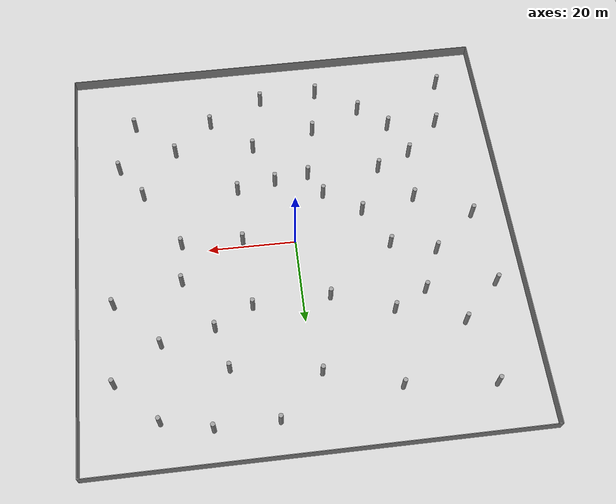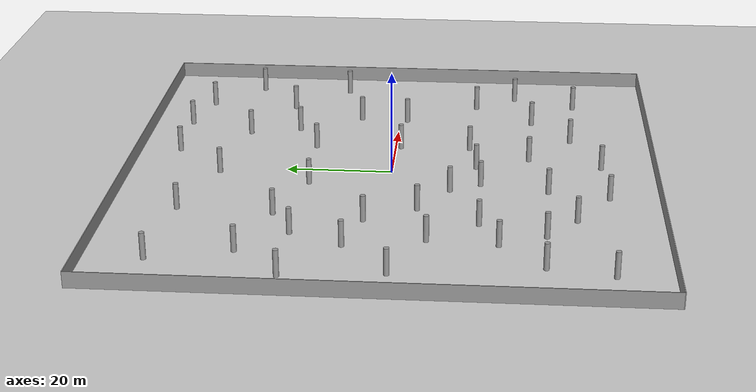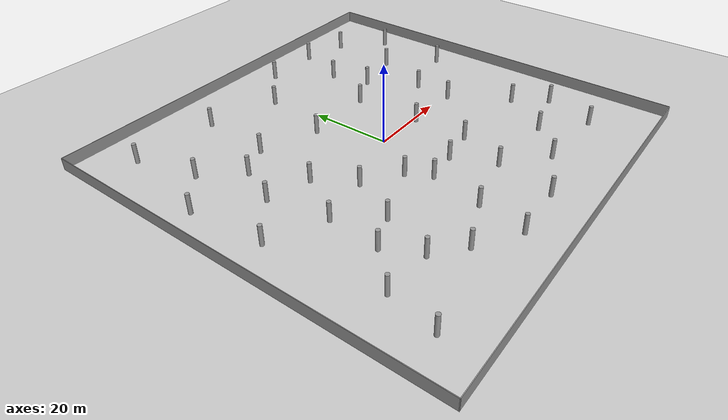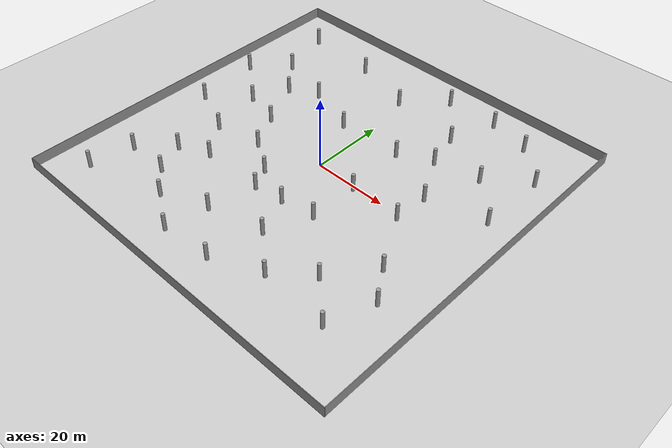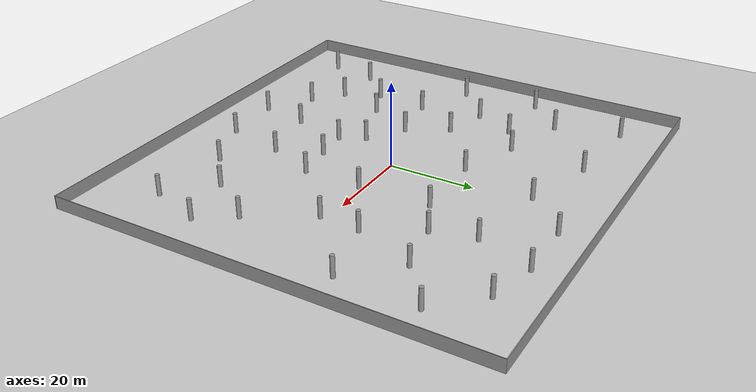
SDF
<sdf version="1.7">
 <world name="default">
  <light name="sun" type="directional">
   <pose>0 0 10 0 -0 0</pose>
   <diffuse>0.8 0.8 0.8 1</diffuse>
   <specular>0.2 0.2 0.2 1</specular>
   <attenuation>
    <range>1000</range>
    <constant>0.9</constant>
    <linear>0.01</linear>
    <quadratic>0.001</quadratic>
   </attenuation>
   <direction>-0.5 0.1 -0.9</direction>
   <spot><inner_angle>0</inner_angle><outer_angle>0</outer_angle><falloff>0</falloff></spot>
  </light>
  <model name="ground_plane">
   <static>1</static>
   <link name="link">
    <collision name="collision">
     <geometry><plane><normal>0 0 1</normal><size>100 100</size></plane></geometry>
     <surface><friction><ode><mu>100</mu><mu2>50</mu2></ode></friction></surface>
    </collision>
    <visual name="visual">
     <cast_shadows>0</cast_shadows>
     <geometry><plane><normal>0 0 1</normal><size>100 100</size></plane></geometry>
     <material>
      <script><uri>file://media/materials/scripts/gazebo.material</uri><name>Gazebo/Grey</name></script>
     </material>
    </visual>
   </link>
  </model>
  <gravity>0 0 -9.8</gravity>
  <magnetic_field>6e-06 2.3e-05 -4.2e-05</magnetic_field>
  <atmosphere type="adiabatic"/>
  <physics type="ode">
   <max_step_size>0.001</max_step_size>
   <real_time_factor>1</real_time_factor>
   <real_time_update_rate>1000</real_time_update_rate>
  </physics>
  <scene><ambient>0.4 0.4 0.4 1</ambient><background>0.7 0.7 0.7 1</background><shadows>1</shadows></scene>
  <spherical_coordinates>
   <surface_model>EARTH_WGS84</surface_model>
   <latitude_deg>0</latitude_deg>
   <longitude_deg>0</longitude_deg>
   <elevation>0</elevation>
   <heading_deg>0</heading_deg>
  </spherical_coordinates>
  <model name="Fence100">
   <link name="Wall_5">
    <collision name="Wall_5_Collision">
     <geometry><box><size>100.15 0.15 3</size></box></geometry>
     <pose>0 0 1.5 0 -0 0</pose>
    </collision>
    <visual name="Wall_5_Visual">
     <pose>0 0 1.5 0 -0 0</pose>
     <geometry><box><size>100.15 0.15 3</size></box></geometry>
     <material>
      <script><uri>file://media/materials/scripts/gazebo.material</uri><name>Gazebo/Grey</name></script>
      <ambient>1 1 1 1</ambient>
     </material>
     <meta><layer>0</layer></meta>
    </visual>
    <pose>-50 0 0 0 -0 1.5708</pose>
   </link>
   <link name="Wall_6">
    <collision name="Wall_6_Collision">
     <geometry><box><size>100.15 0.15 3</size></box></geometry>
     <pose>0 0 1.5 0 -0 0</pose>
    </collision>
    <visual name="Wall_6_Visual">
     <pose>0 0 1.5 0 -0 0</pose>
     <geometry><box><size>100.15 0.15 3</size></box></geometry>
     <material>
      <script><uri>file://media/materials/scripts/gazebo.material</uri><name>Gazebo/Grey</name></script>
      <ambient>1 1 1 1</ambient>
     </material>
     <meta><layer>0</layer></meta>
    </visual>
    <pose>0 50 0 0 -0 0</pose>
   </link>
   <link name="Wall_8">
    <collision name="Wall_8_Collision">
     <geometry><box><size>100.15 0.15 3</size></box></geometry>
     <pose>0 0 1.5 0 -0 0</pose>
    </collision>
    <visual name="Wall_8_Visual">
     <pose>0 0 1.5 0 -0 0</pose>
     <geometry><box><size>100.15 0.15 3</size></box></geometry>
     <material>
      <script><uri>file://media/materials/scripts/gazebo.material</uri><name>Gazebo/Grey</name></script>
      <ambient>1 1 1 1</ambient>
     </material>
     <meta><layer>0</layer></meta>
    </visual>
    <pose>50 0 0 0 -0 -1.5708</pose>
   </link>
   <link name="Wall_9">
    <collision name="Wall_9_Collision">
     <geometry><box><size>100.15 0.15 3</size></box></geometry>
     <pose>0 0 1.5 0 -0 0</pose>
    </collision>
    <visual name="Wall_9_Visual">
     <pose>0 0 1.5 0 -0 0</pose>
     <geometry><box><size>100.15 0.15 3</size></box></geometry>
     <material>
      <script><uri>file://media/materials/scripts/gazebo.material</uri><name>Gazebo/Grey</name></script>
      <ambient>1 1 1 1</ambient>
     </material>
     <meta><layer>0</layer></meta>
    </visual>
    <pose>0 -50 0 0 -0 3.14159</pose>
   </link>
   <static>1</static>
  </model>
  <model name="cylinder5">
   <link name="link">
    <inertial>
     <mass>1</mass>
     <inertia><ixx>0.145833</ixx><ixy>0</ixy><ixz>0</ixz><iyy>0.145833</iyy><iyz>0</iyz><izz>0.125</izz></inertia>
    </inertial>
    <visual name="visual">
     <geometry><cylinder><radius>0.5</radius><length>5</length></cylinder></geometry>
     <material>
      <script><name>Gazebo/Grey</name><uri>file://media/materials/scripts/gazebo.material</uri></script>
      <shader type="pixel"><normal_map>__default__</normal_map></shader>
      <ambient>0.3 0.3 0.3 1</ambient>
      <diffuse>0.7 0.7 0.7 1</diffuse>
      <specular>0.01 0.01 0.01 1</specular>
      <emissive>0 0 0 1</emissive>
     </material>
    </visual>
    <collision name="collision">
     <geometry><cylinder><radius>0.5</radius><length>5</length></cylinder></geometry>
     <surface>
      <friction>
       <ode><mu>1</mu><mu2>1</mu2><fdir1>0 0 0</fdir1><slip1>0</slip1><slip2>0</slip2></ode>
       <torsional>
        <coefficient>1</coefficient>
        <patch_radius>0</patch_radius>
        <surface_radius>0</surface_radius>
        <use_patch_radius>1</use_patch_radius>
        <ode><slip>0</slip></ode>
       </torsional>
      </friction>
      <bounce><restitution_coefficient>0</restitution_coefficient><threshold>1e+06</threshold></bounce>
      <contact>
       <collide_without_contact>0</collide_without_contact>
       <collide_without_contact_bitmask>1</collide_without_contact_bitmask>
       <collide_bitmask>1</collide_bitmask>
       <ode>
        <soft_cfm>0</soft_cfm>
        <soft_erp>0.2</soft_erp>
        <kp>1e+13</kp>
        <kd>1</kd>
        <max_vel>0.01</max_vel>
        <min_depth>0</min_depth>
       </ode>
       <bullet>
        <split_impulse>1</split_impulse>
        <split_impulse_penetration_threshold>-0.01</split_impulse_penetration_threshold>
        <soft_cfm>0</soft_cfm>
        <soft_erp>0.2</soft_erp>
        <kp>1e+13</kp>
        <kd>1</kd>
       </bullet>
      </contact>
     </surface>
    </collision>
   </link>
   <static>0</static>
   <pose>20 20 2.5 0 -0 0</pose>
  </model>
  <model name="cylinder5_clone">
   <link name="link">
    <inertial>
     <mass>1</mass>
     <inertia><ixx>0.145833</ixx><ixy>0</ixy><ixz>0</ixz><iyy>0.145833</iyy><iyz>0</iyz><izz>0.125</izz></inertia>
    </inertial>
    <visual name="visual">
     <geometry><cylinder><radius>0.5</radius><length>5</length></cylinder></geometry>
     <material>
      <script><name>Gazebo/Grey</name><uri>file://media/materials/scripts/gazebo.material</uri></script>
      <shader type="pixel"><normal_map>__default__</normal_map></shader>
      <ambient>0.3 0.3 0.3 1</ambient>
      <diffuse>0.7 0.7 0.7 1</diffuse>
      <specular>0.01 0.01 0.01 1</specular>
      <emissive>0 0 0 1</emissive>
     </material>
    </visual>
    <collision name="collision">
     <geometry><cylinder><radius>0.5</radius><length>5</length></cylinder></geometry>
     <surface>
      <friction>
       <ode><mu>1</mu><mu2>1</mu2><fdir1>0 0 0</fdir1><slip1>0</slip1><slip2>0</slip2></ode>
       <torsional>
        <coefficient>1</coefficient>
        <patch_radius>0</patch_radius>
        <surface_radius>0</surface_radius>
        <use_patch_radius>1</use_patch_radius>
        <ode><slip>0</slip></ode>
       </torsional>
      </friction>
      <bounce><restitution_coefficient>0</restitution_coefficient><threshold>1e+06</threshold></bounce>
      <contact>
       <collide_without_contact>0</collide_without_contact>
       <collide_without_contact_bitmask>1</collide_without_contact_bitmask>
       <collide_bitmask>1</collide_bitmask>
       <ode>
        <soft_cfm>0</soft_cfm>
        <soft_erp>0.2</soft_erp>
        <kp>1e+13</kp>
        <kd>1</kd>
        <max_vel>0.01</max_vel>
        <min_depth>0</min_depth>
       </ode>
       <bullet>
        <split_impulse>1</split_impulse>
        <split_impulse_penetration_threshold>-0.01</split_impulse_penetration_threshold>
        <soft_cfm>0</soft_cfm>
        <soft_erp>0.2</soft_erp>
        <kp>1e+13</kp>
        <kd>1</kd>
       </bullet>
      </contact>
     </surface>
    </collision>
   </link>
   <static>0</static>
   <pose>17.5739 29.7245 2.5 0 -0 0</pose>
  </model>
  <model name="cylinder5_clone_0">
   <link name="link">
    <inertial>
     <mass>1</mass>
     <inertia><ixx>0.145833</ixx><ixy>0</ixy><ixz>0</ixz><iyy>0.145833</iyy><iyz>0</iyz><izz>0.125</izz></inertia>
    </inertial>
    <visual name="visual">
     <geometry><cylinder><radius>0.5</radius><length>5</length></cylinder></geometry>
     <material>
      <script><name>Gazebo/Grey</name><uri>file://media/materials/scripts/gazebo.material</uri></script>
      <shader type="pixel"><normal_map>__default__</normal_map></shader>
      <ambient>0.3 0.3 0.3 1</ambient>
      <diffuse>0.7 0.7 0.7 1</diffuse>
      <specular>0.01 0.01 0.01 1</specular>
      <emissive>0 0 0 1</emissive>
     </material>
    </visual>
    <collision name="collision">
     <geometry><cylinder><radius>0.5</radius><length>5</length></cylinder></geometry>
     <surface>
      <friction>
       <ode><mu>1</mu><mu2>1</mu2><fdir1>0 0 0</fdir1><slip1>0</slip1><slip2>0</slip2></ode>
       <torsional>
        <coefficient>1</coefficient>
        <patch_radius>0</patch_radius>
        <surface_radius>0</surface_radius>
        <use_patch_radius>1</use_patch_radius>
        <ode><slip>0</slip></ode>
       </torsional>
      </friction>
      <bounce><restitution_coefficient>0</restitution_coefficient><threshold>1e+06</threshold></bounce>
      <contact>
       <collide_without_contact>0</collide_without_contact>
       <collide_without_contact_bitmask>1</collide_without_contact_bitmask>
       <collide_bitmask>1</collide_bitmask>
       <ode>
        <soft_cfm>0</soft_cfm>
        <soft_erp>0.2</soft_erp>
        <kp>1e+13</kp>
        <kd>1</kd>
        <max_vel>0.01</max_vel>
        <min_depth>0</min_depth>
       </ode>
       <bullet>
        <split_impulse>1</split_impulse>
        <split_impulse_penetration_threshold>-0.01</split_impulse_penetration_threshold>
        <soft_cfm>0</soft_cfm>
        <soft_erp>0.2</soft_erp>
        <kp>1e+13</kp>
        <kd>1</kd>
       </bullet>
      </contact>
     </surface>
    </collision>
   </link>
   <static>0</static>
   <pose>31.9826 22.4752 2.5 0 -0 0</pose>
  </model>
  <model name="cylinder5_clone_1">
   <link name="link">
    <inertial>
     <mass>1</mass>
     <inertia><ixx>0.145833</ixx><ixy>0</ixy><ixz>0</ixz><iyy>0.145833</iyy><iyz>0</iyz><izz>0.125</izz></inertia>
    </inertial>
    <visual name="visual">
     <geometry><cylinder><radius>0.5</radius><length>5</length></cylinder></geometry>
     <material>
      <script><name>Gazebo/Grey</name><uri>file://media/materials/scripts/gazebo.material</uri></script>
      <shader type="pixel"><normal_map>__default__</normal_map></shader>
      <ambient>0.3 0.3 0.3 1</ambient>
      <diffuse>0.7 0.7 0.7 1</diffuse>
      <specular>0.01 0.01 0.01 1</specular>
      <emissive>0 0 0 1</emissive>
     </material>
    </visual>
    <collision name="collision">
     <geometry><cylinder><radius>0.5</radius><length>5</length></cylinder></geometry>
     <surface>
      <friction>
       <ode><mu>1</mu><mu2>1</mu2><fdir1>0 0 0</fdir1><slip1>0</slip1><slip2>0</slip2></ode>
       <torsional>
        <coefficient>1</coefficient>
        <patch_radius>0</patch_radius>
        <surface_radius>0</surface_radius>
        <use_patch_radius>1</use_patch_radius>
        <ode><slip>0</slip></ode>
       </torsional>
      </friction>
      <bounce><restitution_coefficient>0</restitution_coefficient><threshold>1e+06</threshold></bounce>
      <contact>
       <collide_without_contact>0</collide_without_contact>
       <collide_without_contact_bitmask>1</collide_without_contact_bitmask>
       <collide_bitmask>1</collide_bitmask>
       <ode>
        <soft_cfm>0</soft_cfm>
        <soft_erp>0.2</soft_erp>
        <kp>1e+13</kp>
        <kd>1</kd>
        <max_vel>0.01</max_vel>
        <min_depth>0</min_depth>
       </ode>
       <bullet>
        <split_impulse>1</split_impulse>
        <split_impulse_penetration_threshold>-0.01</split_impulse_penetration_threshold>
        <soft_cfm>0</soft_cfm>
        <soft_erp>0.2</soft_erp>
        <kp>1e+13</kp>
        <kd>1</kd>
       </bullet>
      </contact>
     </surface>
    </collision>
   </link>
   <static>0</static>
   <pose>26.0453 -1.37565 2.5 0 -0 0</pose>
  </model>
  <model name="cylinder5_clone_2">
   <link name="link">
    <inertial>
     <mass>1</mass>
     <inertia><ixx>0.145833</ixx><ixy>0</ixy><ixz>0</ixz><iyy>0.145833</iyy><iyz>0</iyz><izz>0.125</izz></inertia>
    </inertial>
    <visual name="visual">
     <geometry><cylinder><radius>0.5</radius><length>5</length></cylinder></geometry>
     <material>
      <script><name>Gazebo/Grey</name><uri>file://media/materials/scripts/gazebo.material</uri></script>
      <shader type="pixel"><normal_map>__default__</normal_map></shader>
      <ambient>0.3 0.3 0.3 1</ambient>
      <diffuse>0.7 0.7 0.7 1</diffuse>
      <specular>0.01 0.01 0.01 1</specular>
      <emissive>0 0 0 1</emissive>
     </material>
    </visual>
    <collision name="collision">
     <geometry><cylinder><radius>0.5</radius><length>5</length></cylinder></geometry>
     <surface>
      <friction>
       <ode><mu>1</mu><mu2>1</mu2><fdir1>0 0 0</fdir1><slip1>0</slip1><slip2>0</slip2></ode>
       <torsional>
        <coefficient>1</coefficient>
        <patch_radius>0</patch_radius>
        <surface_radius>0</surface_radius>
        <use_patch_radius>1</use_patch_radius>
        <ode><slip>0</slip></ode>
       </torsional>
      </friction>
      <bounce><restitution_coefficient>0</restitution_coefficient><threshold>1e+06</threshold></bounce>
      <contact>
       <collide_without_contact>0</collide_without_contact>
       <collide_without_contact_bitmask>1</collide_without_contact_bitmask>
       <collide_bitmask>1</collide_bitmask>
       <ode>
        <soft_cfm>0</soft_cfm>
        <soft_erp>0.2</soft_erp>
        <kp>1e+13</kp>
        <kd>1</kd>
        <max_vel>0.01</max_vel>
        <min_depth>0</min_depth>
       </ode>
       <bullet>
        <split_impulse>1</split_impulse>
        <split_impulse_penetration_threshold>-0.01</split_impulse_penetration_threshold>
        <soft_cfm>0</soft_cfm>
        <soft_erp>0.2</soft_erp>
        <kp>1e+13</kp>
        <kd>1</kd>
       </bullet>
      </contact>
     </surface>
    </collision>
   </link>
   <static>0</static>
   <pose>26.5297 7.97836 2.5 0 -0 0</pose>
  </model>
  <model name="cylinder5_clone_3">
   <link name="link">
    <inertial>
     <mass>1</mass>
     <inertia><ixx>0.145833</ixx><ixy>0</ixy><ixz>0</ixz><iyy>0.145833</iyy><iyz>0</iyz><izz>0.125</izz></inertia>
    </inertial>
    <visual name="visual">
     <geometry><cylinder><radius>0.5</radius><length>5</length></cylinder></geometry>
     <material>
      <script><name>Gazebo/Grey</name><uri>file://media/materials/scripts/gazebo.material</uri></script>
      <shader type="pixel"><normal_map>__default__</normal_map></shader>
      <ambient>0.3 0.3 0.3 1</ambient>
      <diffuse>0.7 0.7 0.7 1</diffuse>
      <specular>0.01 0.01 0.01 1</specular>
      <emissive>0 0 0 1</emissive>
     </material>
    </visual>
    <collision name="collision">
     <geometry><cylinder><radius>0.5</radius><length>5</length></cylinder></geometry>
     <surface>
      <friction>
       <ode><mu>1</mu><mu2>1</mu2><fdir1>0 0 0</fdir1><slip1>0</slip1><slip2>0</slip2></ode>
       <torsional>
        <coefficient>1</coefficient>
        <patch_radius>0</patch_radius>
        <surface_radius>0</surface_radius>
        <use_patch_radius>1</use_patch_radius>
        <ode><slip>0</slip></ode>
       </torsional>
      </friction>
      <bounce><restitution_coefficient>0</restitution_coefficient><threshold>1e+06</threshold></bounce>
      <contact>
       <collide_without_contact>0</collide_without_contact>
       <collide_without_contact_bitmask>1</collide_without_contact_bitmask>
       <collide_bitmask>1</collide_bitmask>
       <ode>
        <soft_cfm>0</soft_cfm>
        <soft_erp>0.2</soft_erp>
        <kp>1e+13</kp>
        <kd>1</kd>
        <max_vel>0.01</max_vel>
        <min_depth>0</min_depth>
       </ode>
       <bullet>
        <split_impulse>1</split_impulse>
        <split_impulse_penetration_threshold>-0.01</split_impulse_penetration_threshold>
        <soft_cfm>0</soft_cfm>
        <soft_erp>0.2</soft_erp>
        <kp>1e+13</kp>
        <kd>1</kd>
       </bullet>
      </contact>
     </surface>
    </collision>
   </link>
   <static>0</static>
   <pose>-27.5667 16 2.5 0 -0 0</pose>
  </model>
  <model name="cylinder5_clone_4">
   <link name="link">
    <inertial>
     <mass>1</mass>
     <inertia><ixx>0.145833</ixx><ixy>0</ixy><ixz>0</ixz><iyy>0.145833</iyy><iyz>0</iyz><izz>0.125</izz></inertia>
    </inertial>
    <visual name="visual">
     <geometry><cylinder><radius>0.5</radius><length>5</length></cylinder></geometry>
     <material>
      <script><name>Gazebo/Grey</name><uri>file://media/materials/scripts/gazebo.material</uri></script>
      <shader type="pixel"><normal_map>__default__</normal_map></shader>
      <ambient>0.3 0.3 0.3 1</ambient>
      <diffuse>0.7 0.7 0.7 1</diffuse>
      <specular>0.01 0.01 0.01 1</specular>
      <emissive>0 0 0 1</emissive>
     </material>
    </visual>
    <collision name="collision">
     <geometry><cylinder><radius>0.5</radius><length>5</length></cylinder></geometry>
     <surface>
      <friction>
       <ode><mu>1</mu><mu2>1</mu2><fdir1>0 0 0</fdir1><slip1>0</slip1><slip2>0</slip2></ode>
       <torsional>
        <coefficient>1</coefficient>
        <patch_radius>0</patch_radius>
        <surface_radius>0</surface_radius>
        <use_patch_radius>1</use_patch_radius>
        <ode><slip>0</slip></ode>
       </torsional>
      </friction>
      <bounce><restitution_coefficient>0</restitution_coefficient><threshold>1e+06</threshold></bounce>
      <contact>
       <collide_without_contact>0</collide_without_contact>
       <collide_without_contact_bitmask>1</collide_without_contact_bitmask>
       <collide_bitmask>1</collide_bitmask>
       <ode>
        <soft_cfm>0</soft_cfm>
        <soft_erp>0.2</soft_erp>
        <kp>1e+13</kp>
        <kd>1</kd>
        <max_vel>0.01</max_vel>
        <min_depth>0</min_depth>
       </ode>
       <bullet>
        <split_impulse>1</split_impulse>
        <split_impulse_penetration_threshold>-0.01</split_impulse_penetration_threshold>
        <soft_cfm>0</soft_cfm>
        <soft_erp>0.2</soft_erp>
        <kp>1e+13</kp>
        <kd>1</kd>
       </bullet>
      </contact>
     </surface>
    </collision>
   </link>
   <static>0</static>
   <pose>-20 20 2.5 0 -0 0</pose>
  </model>
  <model name="cylinder5_clone_5">
   <link name="link">
    <inertial>
     <mass>1</mass>
     <inertia><ixx>0.145833</ixx><ixy>0</ixy><ixz>0</ixz><iyy>0.145833</iyy><iyz>0</iyz><izz>0.125</izz></inertia>
    </inertial>
    <visual name="visual">
     <geometry><cylinder><radius>0.5</radius><length>5</length></cylinder></geometry>
     <material>
      <script><name>Gazebo/Grey</name><uri>file://media/materials/scripts/gazebo.material</uri></script>
      <shader type="pixel"><normal_map>__default__</normal_map></shader>
      <ambient>0.3 0.3 0.3 1</ambient>
      <diffuse>0.7 0.7 0.7 1</diffuse>
      <specular>0.01 0.01 0.01 1</specular>
      <emissive>0 0 0 1</emissive>
     </material>
    </visual>
    <collision name="collision">
     <geometry><cylinder><radius>0.5</radius><length>5</length></cylinder></geometry>
     <surface>
      <friction>
       <ode><mu>1</mu><mu2>1</mu2><fdir1>0 0 0</fdir1><slip1>0</slip1><slip2>0</slip2></ode>
       <torsional>
        <coefficient>1</coefficient>
        <patch_radius>0</patch_radius>
        <surface_radius>0</surface_radius>
        <use_patch_radius>1</use_patch_radius>
        <ode><slip>0</slip></ode>
       </torsional>
      </friction>
      <bounce><restitution_coefficient>0</restitution_coefficient><threshold>1e+06</threshold></bounce>
      <contact>
       <collide_without_contact>0</collide_without_contact>
       <collide_without_contact_bitmask>1</collide_without_contact_bitmask>
       <collide_bitmask>1</collide_bitmask>
       <ode>
        <soft_cfm>0</soft_cfm>
        <soft_erp>0.2</soft_erp>
        <kp>1e+13</kp>
        <kd>1</kd>
        <max_vel>0.01</max_vel>
        <min_depth>0</min_depth>
       </ode>
       <bullet>
        <split_impulse>1</split_impulse>
        <split_impulse_penetration_threshold>-0.01</split_impulse_penetration_threshold>
        <soft_cfm>0</soft_cfm>
        <soft_erp>0.2</soft_erp>
        <kp>1e+13</kp>
        <kd>1</kd>
       </bullet>
      </contact>
     </surface>
    </collision>
   </link>
   <static>0</static>
   <pose>-21.6145 3.6114 2.5 0 -0 0</pose>
  </model>
  <model name="cylinder5_clone_6">
   <link name="link">
    <inertial>
     <mass>1</mass>
     <inertia><ixx>0.145833</ixx><ixy>0</ixy><ixz>0</ixz><iyy>0.145833</iyy><iyz>0</iyz><izz>0.125</izz></inertia>
    </inertial>
    <visual name="visual">
     <geometry><cylinder><radius>0.5</radius><length>5</length></cylinder></geometry>
     <material>
      <script><name>Gazebo/Grey</name><uri>file://media/materials/scripts/gazebo.material</uri></script>
      <shader type="pixel"><normal_map>__default__</normal_map></shader>
      <ambient>0.3 0.3 0.3 1</ambient>
      <diffuse>0.7 0.7 0.7 1</diffuse>
      <specular>0.01 0.01 0.01 1</specular>
      <emissive>0 0 0 1</emissive>
     </material>
    </visual>
    <collision name="collision">
     <geometry><cylinder><radius>0.5</radius><length>5</length></cylinder></geometry>
     <surface>
      <friction>
       <ode><mu>1</mu><mu2>1</mu2><fdir1>0 0 0</fdir1><slip1>0</slip1><slip2>0</slip2></ode>
       <torsional>
        <coefficient>1</coefficient>
        <patch_radius>0</patch_radius>
        <surface_radius>0</surface_radius>
        <use_patch_radius>1</use_patch_radius>
        <ode><slip>0</slip></ode>
       </torsional>
      </friction>
      <bounce><restitution_coefficient>0</restitution_coefficient><threshold>1e+06</threshold></bounce>
      <contact>
       <collide_without_contact>0</collide_without_contact>
       <collide_without_contact_bitmask>1</collide_without_contact_bitmask>
       <collide_bitmask>1</collide_bitmask>
       <ode>
        <soft_cfm>0</soft_cfm>
        <soft_erp>0.2</soft_erp>
        <kp>1e+13</kp>
        <kd>1</kd>
        <max_vel>0.01</max_vel>
        <min_depth>0</min_depth>
       </ode>
       <bullet>
        <split_impulse>1</split_impulse>
        <split_impulse_penetration_threshold>-0.01</split_impulse_penetration_threshold>
        <soft_cfm>0</soft_cfm>
        <soft_erp>0.2</soft_erp>
        <kp>1e+13</kp>
        <kd>1</kd>
       </bullet>
      </contact>
     </surface>
    </collision>
   </link>
   <static>0</static>
   <pose>-29 -8 2.5 0 -0 0</pose>
  </model>
  <model name="cylinder5_clone_7">
   <link name="link">
    <inertial>
     <mass>1</mass>
     <inertia><ixx>0.145833</ixx><ixy>0</ixy><ixz>0</ixz><iyy>0.145833</iyy><iyz>0</iyz><izz>0.125</izz></inertia>
    </inertial>
    <visual name="visual">
     <geometry><cylinder><radius>0.5</radius><length>5</length></cylinder></geometry>
     <material>
      <script><name>Gazebo/Grey</name><uri>file://media/materials/scripts/gazebo.material</uri></script>
      <shader type="pixel"><normal_map>__default__</normal_map></shader>
      <ambient>0.3 0.3 0.3 1</ambient>
      <diffuse>0.7 0.7 0.7 1</diffuse>
      <specular>0.01 0.01 0.01 1</specular>
      <emissive>0 0 0 1</emissive>
     </material>
    </visual>
    <collision name="collision">
     <geometry><cylinder><radius>0.5</radius><length>5</length></cylinder></geometry>
     <surface>
      <friction>
       <ode><mu>1</mu><mu2>1</mu2><fdir1>0 0 0</fdir1><slip1>0</slip1><slip2>0</slip2></ode>
       <torsional>
        <coefficient>1</coefficient>
        <patch_radius>0</patch_radius>
        <surface_radius>0</surface_radius>
        <use_patch_radius>1</use_patch_radius>
        <ode><slip>0</slip></ode>
       </torsional>
      </friction>
      <bounce><restitution_coefficient>0</restitution_coefficient><threshold>1e+06</threshold></bounce>
      <contact>
       <collide_without_contact>0</collide_without_contact>
       <collide_without_contact_bitmask>1</collide_without_contact_bitmask>
       <collide_bitmask>1</collide_bitmask>
       <ode>
        <soft_cfm>0</soft_cfm>
        <soft_erp>0.2</soft_erp>
        <kp>1e+13</kp>
        <kd>1</kd>
        <max_vel>0.01</max_vel>
        <min_depth>0</min_depth>
       </ode>
       <bullet>
        <split_impulse>1</split_impulse>
        <split_impulse_penetration_threshold>-0.01</split_impulse_penetration_threshold>
        <soft_cfm>0</soft_cfm>
        <soft_erp>0.2</soft_erp>
        <kp>1e+13</kp>
        <kd>1</kd>
       </bullet>
      </contact>
     </surface>
    </collision>
   </link>
   <static>0</static>
   <pose>-31.8324 6.42922 2.5 0 -0 0</pose>
  </model>
  <model name="cylinder5_clone_8">
   <link name="link">
    <inertial>
     <mass>1</mass>
     <inertia><ixx>0.145833</ixx><ixy>0</ixy><ixz>0</ixz><iyy>0.145833</iyy><iyz>0</iyz><izz>0.125</izz></inertia>
    </inertial>
    <visual name="visual">
     <geometry><cylinder><radius>0.5</radius><length>5</length></cylinder></geometry>
     <material>
      <script><name>Gazebo/Grey</name><uri>file://media/materials/scripts/gazebo.material</uri></script>
      <shader type="pixel"><normal_map>__default__</normal_map></shader>
      <ambient>0.3 0.3 0.3 1</ambient>
      <diffuse>0.7 0.7 0.7 1</diffuse>
      <specular>0.01 0.01 0.01 1</specular>
      <emissive>0 0 0 1</emissive>
     </material>
    </visual>
    <collision name="collision">
     <geometry><cylinder><radius>0.5</radius><length>5</length></cylinder></geometry>
     <surface>
      <friction>
       <ode><mu>1</mu><mu2>1</mu2><fdir1>0 0 0</fdir1><slip1>0</slip1><slip2>0</slip2></ode>
       <torsional>
        <coefficient>1</coefficient>
        <patch_radius>0</patch_radius>
        <surface_radius>0</surface_radius>
        <use_patch_radius>1</use_patch_radius>
        <ode><slip>0</slip></ode>
       </torsional>
      </friction>
      <bounce><restitution_coefficient>0</restitution_coefficient><threshold>1e+06</threshold></bounce>
      <contact>
       <collide_without_contact>0</collide_without_contact>
       <collide_without_contact_bitmask>1</collide_without_contact_bitmask>
       <collide_bitmask>1</collide_bitmask>
       <ode>
        <soft_cfm>0</soft_cfm>
        <soft_erp>0.2</soft_erp>
        <kp>1e+13</kp>
        <kd>1</kd>
        <max_vel>0.01</max_vel>
        <min_depth>0</min_depth>
       </ode>
       <bullet>
        <split_impulse>1</split_impulse>
        <split_impulse_penetration_threshold>-0.01</split_impulse_penetration_threshold>
        <soft_cfm>0</soft_cfm>
        <soft_erp>0.2</soft_erp>
        <kp>1e+13</kp>
        <kd>1</kd>
       </bullet>
      </contact>
     </surface>
    </collision>
   </link>
   <static>0</static>
   <pose>-35.0392 24.4897 2.5 0 -0 0</pose>
  </model>
  <model name="cylinder5_clone_9">
   <link name="link">
    <inertial>
     <mass>1</mass>
     <inertia><ixx>0.145833</ixx><ixy>0</ixy><ixz>0</ixz><iyy>0.145833</iyy><iyz>0</iyz><izz>0.125</izz></inertia>
    </inertial>
    <visual name="visual">
     <geometry><cylinder><radius>0.5</radius><length>5</length></cylinder></geometry>
     <material>
      <script><name>Gazebo/Grey</name><uri>file://media/materials/scripts/gazebo.material</uri></script>
      <shader type="pixel"><normal_map>__default__</normal_map></shader>
      <ambient>0.3 0.3 0.3 1</ambient>
      <diffuse>0.7 0.7 0.7 1</diffuse>
      <specular>0.01 0.01 0.01 1</specular>
      <emissive>0 0 0 1</emissive>
     </material>
    </visual>
    <collision name="collision">
     <geometry><cylinder><radius>0.5</radius><length>5</length></cylinder></geometry>
     <surface>
      <friction>
       <ode><mu>1</mu><mu2>1</mu2><fdir1>0 0 0</fdir1><slip1>0</slip1><slip2>0</slip2></ode>
       <torsional>
        <coefficient>1</coefficient>
        <patch_radius>0</patch_radius>
        <surface_radius>0</surface_radius>
        <use_patch_radius>1</use_patch_radius>
        <ode><slip>0</slip></ode>
       </torsional>
      </friction>
      <bounce><restitution_coefficient>0</restitution_coefficient><threshold>1e+06</threshold></bounce>
      <contact>
       <collide_without_contact>0</collide_without_contact>
       <collide_without_contact_bitmask>1</collide_without_contact_bitmask>
       <collide_bitmask>1</collide_bitmask>
       <ode>
        <soft_cfm>0</soft_cfm>
        <soft_erp>0.2</soft_erp>
        <kp>1e+13</kp>
        <kd>1</kd>
        <max_vel>0.01</max_vel>
        <min_depth>0</min_depth>
       </ode>
       <bullet>
        <split_impulse>1</split_impulse>
        <split_impulse_penetration_threshold>-0.01</split_impulse_penetration_threshold>
        <soft_cfm>0</soft_cfm>
        <soft_erp>0.2</soft_erp>
        <kp>1e+13</kp>
        <kd>1</kd>
       </bullet>
      </contact>
     </surface>
    </collision>
   </link>
   <static>0</static>
   <pose>-2.13208 32.6685 2.5 0 -0 0</pose>
  </model>
  <model name="cylinder5_clone_10">
   <link name="link">
    <inertial>
     <mass>1</mass>
     <inertia><ixx>0.145833</ixx><ixy>0</ixy><ixz>0</ixz><iyy>0.145833</iyy><iyz>0</iyz><izz>0.125</izz></inertia>
    </inertial>
    <visual name="visual">
     <geometry><cylinder><radius>0.5</radius><length>5</length></cylinder></geometry>
     <material>
      <script><name>Gazebo/Grey</name><uri>file://media/materials/scripts/gazebo.material</uri></script>
      <shader type="pixel"><normal_map>__default__</normal_map></shader>
      <ambient>0.3 0.3 0.3 1</ambient>
      <diffuse>0.7 0.7 0.7 1</diffuse>
      <specular>0.01 0.01 0.01 1</specular>
      <emissive>0 0 0 1</emissive>
     </material>
    </visual>
    <collision name="collision">
     <geometry><cylinder><radius>0.5</radius><length>5</length></cylinder></geometry>
     <surface>
      <friction>
       <ode><mu>1</mu><mu2>1</mu2><fdir1>0 0 0</fdir1><slip1>0</slip1><slip2>0</slip2></ode>
       <torsional>
        <coefficient>1</coefficient>
        <patch_radius>0</patch_radius>
        <surface_radius>0</surface_radius>
        <use_patch_radius>1</use_patch_radius>
        <ode><slip>0</slip></ode>
       </torsional>
      </friction>
      <bounce><restitution_coefficient>0</restitution_coefficient><threshold>1e+06</threshold></bounce>
      <contact>
       <collide_without_contact>0</collide_without_contact>
       <collide_without_contact_bitmask>1</collide_without_contact_bitmask>
       <collide_bitmask>1</collide_bitmask>
       <ode>
        <soft_cfm>0</soft_cfm>
        <soft_erp>0.2</soft_erp>
        <kp>1e+13</kp>
        <kd>1</kd>
        <max_vel>0.01</max_vel>
        <min_depth>0</min_depth>
       </ode>
       <bullet>
        <split_impulse>1</split_impulse>
        <split_impulse_penetration_threshold>-0.01</split_impulse_penetration_threshold>
        <soft_cfm>0</soft_cfm>
        <soft_erp>0.2</soft_erp>
        <kp>1e+13</kp>
        <kd>1</kd>
       </bullet>
      </contact>
     </surface>
    </collision>
   </link>
   <static>0</static>
   <pose>-18.8484 37.6461 2.5 0 -0 0</pose>
  </model>
  <model name="cylinder5_clone_11">
   <link name="link">
    <inertial>
     <mass>1</mass>
     <inertia><ixx>0.145833</ixx><ixy>0</ixy><ixz>0</ixz><iyy>0.145833</iyy><iyz>0</iyz><izz>0.125</izz></inertia>
    </inertial>
    <visual name="visual">
     <geometry><cylinder><radius>0.5</radius><length>5</length></cylinder></geometry>
     <material>
      <script><name>Gazebo/Grey</name><uri>file://media/materials/scripts/gazebo.material</uri></script>
      <shader type="pixel"><normal_map>__default__</normal_map></shader>
      <ambient>0.3 0.3 0.3 1</ambient>
      <diffuse>0.7 0.7 0.7 1</diffuse>
      <specular>0.01 0.01 0.01 1</specular>
      <emissive>0 0 0 1</emissive>
     </material>
    </visual>
    <collision name="collision">
     <geometry><cylinder><radius>0.5</radius><length>5</length></cylinder></geometry>
     <surface>
      <friction>
       <ode><mu>1</mu><mu2>1</mu2><fdir1>0 0 0</fdir1><slip1>0</slip1><slip2>0</slip2></ode>
       <torsional>
        <coefficient>1</coefficient>
        <patch_radius>0</patch_radius>
        <surface_radius>0</surface_radius>
        <use_patch_radius>1</use_patch_radius>
        <ode><slip>0</slip></ode>
       </torsional>
      </friction>
      <bounce><restitution_coefficient>0</restitution_coefficient><threshold>1e+06</threshold></bounce>
      <contact>
       <collide_without_contact>0</collide_without_contact>
       <collide_without_contact_bitmask>1</collide_without_contact_bitmask>
       <collide_bitmask>1</collide_bitmask>
       <ode>
        <soft_cfm>0</soft_cfm>
        <soft_erp>0.2</soft_erp>
        <kp>1e+13</kp>
        <kd>1</kd>
        <max_vel>0.01</max_vel>
        <min_depth>0</min_depth>
       </ode>
       <bullet>
        <split_impulse>1</split_impulse>
        <split_impulse_penetration_threshold>-0.01</split_impulse_penetration_threshold>
        <soft_cfm>0</soft_cfm>
        <soft_erp>0.2</soft_erp>
        <kp>1e+13</kp>
        <kd>1</kd>
       </bullet>
      </contact>
     </surface>
    </collision>
   </link>
   <static>0</static>
   <pose>-6.20234 15.1079 2.5 0 -0 0</pose>
  </model>
  <model name="cylinder5_clone_12">
   <link name="link">
    <inertial>
     <mass>1</mass>
     <inertia><ixx>0.145833</ixx><ixy>0</ixy><ixz>0</ixz><iyy>0.145833</iyy><iyz>0</iyz><izz>0.125</izz></inertia>
    </inertial>
    <visual name="visual">
     <geometry><cylinder><radius>0.5</radius><length>5</length></cylinder></geometry>
     <material>
      <script><name>Gazebo/Grey</name><uri>file://media/materials/scripts/gazebo.material</uri></script>
      <shader type="pixel"><normal_map>__default__</normal_map></shader>
      <ambient>0.3 0.3 0.3 1</ambient>
      <diffuse>0.7 0.7 0.7 1</diffuse>
      <specular>0.01 0.01 0.01 1</specular>
      <emissive>0 0 0 1</emissive>
     </material>
    </visual>
    <collision name="collision">
     <geometry><cylinder><radius>0.5</radius><length>5</length></cylinder></geometry>
     <surface>
      <friction>
       <ode><mu>1</mu><mu2>1</mu2><fdir1>0 0 0</fdir1><slip1>0</slip1><slip2>0</slip2></ode>
       <torsional>
        <coefficient>1</coefficient>
        <patch_radius>0</patch_radius>
        <surface_radius>0</surface_radius>
        <use_patch_radius>1</use_patch_radius>
        <ode><slip>0</slip></ode>
       </torsional>
      </friction>
      <bounce><restitution_coefficient>0</restitution_coefficient><threshold>1e+06</threshold></bounce>
      <contact>
       <collide_without_contact>0</collide_without_contact>
       <collide_without_contact_bitmask>1</collide_without_contact_bitmask>
       <collide_bitmask>1</collide_bitmask>
       <ode>
        <soft_cfm>0</soft_cfm>
        <soft_erp>0.2</soft_erp>
        <kp>1e+13</kp>
        <kd>1</kd>
        <max_vel>0.01</max_vel>
        <min_depth>0</min_depth>
       </ode>
       <bullet>
        <split_impulse>1</split_impulse>
        <split_impulse_penetration_threshold>-0.01</split_impulse_penetration_threshold>
        <soft_cfm>0</soft_cfm>
        <soft_erp>0.2</soft_erp>
        <kp>1e+13</kp>
        <kd>1</kd>
       </bullet>
      </contact>
     </surface>
    </collision>
   </link>
   <static>0</static>
   <pose>11.2799 15.6577 2.5 0 -0 0</pose>
  </model>
  <model name="cylinder5_clone_13">
   <link name="link">
    <inertial>
     <mass>1</mass>
     <inertia><ixx>0.145833</ixx><ixy>0</ixy><ixz>0</ixz><iyy>0.145833</iyy><iyz>0</iyz><izz>0.125</izz></inertia>
    </inertial>
    <visual name="visual">
     <geometry><cylinder><radius>0.5</radius><length>5</length></cylinder></geometry>
     <material>
      <script><name>Gazebo/Grey</name><uri>file://media/materials/scripts/gazebo.material</uri></script>
      <shader type="pixel"><normal_map>__default__</normal_map></shader>
      <ambient>0.3 0.3 0.3 1</ambient>
      <diffuse>0.7 0.7 0.7 1</diffuse>
      <specular>0.01 0.01 0.01 1</specular>
      <emissive>0 0 0 1</emissive>
     </material>
    </visual>
    <collision name="collision">
     <geometry><cylinder><radius>0.5</radius><length>5</length></cylinder></geometry>
     <surface>
      <friction>
       <ode><mu>1</mu><mu2>1</mu2><fdir1>0 0 0</fdir1><slip1>0</slip1><slip2>0</slip2></ode>
       <torsional>
        <coefficient>1</coefficient>
        <patch_radius>0</patch_radius>
        <surface_radius>0</surface_radius>
        <use_patch_radius>1</use_patch_radius>
        <ode><slip>0</slip></ode>
       </torsional>
      </friction>
      <bounce><restitution_coefficient>0</restitution_coefficient><threshold>1e+06</threshold></bounce>
      <contact>
       <collide_without_contact>0</collide_without_contact>
       <collide_without_contact_bitmask>1</collide_without_contact_bitmask>
       <collide_bitmask>1</collide_bitmask>
       <ode>
        <soft_cfm>0</soft_cfm>
        <soft_erp>0.2</soft_erp>
        <kp>1e+13</kp>
        <kd>1</kd>
        <max_vel>0.01</max_vel>
        <min_depth>0</min_depth>
       </ode>
       <bullet>
        <split_impulse>1</split_impulse>
        <split_impulse_penetration_threshold>-0.01</split_impulse_penetration_threshold>
        <soft_cfm>0</soft_cfm>
        <soft_erp>0.2</soft_erp>
        <kp>1e+13</kp>
        <kd>1</kd>
       </bullet>
      </contact>
     </surface>
    </collision>
   </link>
   <static>0</static>
   <pose>12 -1 2.5 0 -0 0</pose>
  </model>
  <model name="cylinder5_clone_14">
   <link name="link">
    <inertial>
     <mass>1</mass>
     <inertia><ixx>0.145833</ixx><ixy>0</ixy><ixz>0</ixz><iyy>0.145833</iyy><iyz>0</iyz><izz>0.125</izz></inertia>
    </inertial>
    <visual name="visual">
     <geometry><cylinder><radius>0.5</radius><length>5</length></cylinder></geometry>
     <material>
      <script><name>Gazebo/Grey</name><uri>file://media/materials/scripts/gazebo.material</uri></script>
      <shader type="pixel"><normal_map>__default__</normal_map></shader>
      <ambient>0.3 0.3 0.3 1</ambient>
      <diffuse>0.7 0.7 0.7 1</diffuse>
      <specular>0.01 0.01 0.01 1</specular>
      <emissive>0 0 0 1</emissive>
     </material>
    </visual>
    <collision name="collision">
     <geometry><cylinder><radius>0.5</radius><length>5</length></cylinder></geometry>
     <surface>
      <friction>
       <ode><mu>1</mu><mu2>1</mu2><fdir1>0 0 0</fdir1><slip1>0</slip1><slip2>0</slip2></ode>
       <torsional>
        <coefficient>1</coefficient>
        <patch_radius>0</patch_radius>
        <surface_radius>0</surface_radius>
        <use_patch_radius>1</use_patch_radius>
        <ode><slip>0</slip></ode>
       </torsional>
      </friction>
      <bounce><restitution_coefficient>0</restitution_coefficient><threshold>1e+06</threshold></bounce>
      <contact>
       <collide_without_contact>0</collide_without_contact>
       <collide_without_contact_bitmask>1</collide_without_contact_bitmask>
       <collide_bitmask>1</collide_bitmask>
       <ode>
        <soft_cfm>0</soft_cfm>
        <soft_erp>0.2</soft_erp>
        <kp>1e+13</kp>
        <kd>1</kd>
        <max_vel>0.01</max_vel>
        <min_depth>0</min_depth>
       </ode>
       <bullet>
        <split_impulse>1</split_impulse>
        <split_impulse_penetration_threshold>-0.01</split_impulse_penetration_threshold>
        <soft_cfm>0</soft_cfm>
        <soft_erp>0.2</soft_erp>
        <kp>1e+13</kp>
        <kd>1</kd>
       </bullet>
      </contact>
     </surface>
    </collision>
   </link>
   <static>0</static>
   <pose>12.0182 -14.5473 2.5 0 -0 0</pose>
  </model>
  <model name="cylinder5_clone_15">
   <link name="link">
    <inertial>
     <mass>1</mass>
     <inertia><ixx>0.145833</ixx><ixy>0</ixy><ixz>0</ixz><iyy>0.145833</iyy><iyz>0</iyz><izz>0.125</izz></inertia>
    </inertial>
    <visual name="visual">
     <geometry><cylinder><radius>0.5</radius><length>5</length></cylinder></geometry>
     <material>
      <script><name>Gazebo/Grey</name><uri>file://media/materials/scripts/gazebo.material</uri></script>
      <shader type="pixel"><normal_map>__default__</normal_map></shader>
      <ambient>0.3 0.3 0.3 1</ambient>
      <diffuse>0.7 0.7 0.7 1</diffuse>
      <specular>0.01 0.01 0.01 1</specular>
      <emissive>0 0 0 1</emissive>
     </material>
    </visual>
    <collision name="collision">
     <geometry><cylinder><radius>0.5</radius><length>5</length></cylinder></geometry>
     <surface>
      <friction>
       <ode><mu>1</mu><mu2>1</mu2><fdir1>0 0 0</fdir1><slip1>0</slip1><slip2>0</slip2></ode>
       <torsional>
        <coefficient>1</coefficient>
        <patch_radius>0</patch_radius>
        <surface_radius>0</surface_radius>
        <use_patch_radius>1</use_patch_radius>
        <ode><slip>0</slip></ode>
       </torsional>
      </friction>
      <bounce><restitution_coefficient>0</restitution_coefficient><threshold>1e+06</threshold></bounce>
      <contact>
       <collide_without_contact>0</collide_without_contact>
       <collide_without_contact_bitmask>1</collide_without_contact_bitmask>
       <collide_bitmask>1</collide_bitmask>
       <ode>
        <soft_cfm>0</soft_cfm>
        <soft_erp>0.2</soft_erp>
        <kp>1e+13</kp>
        <kd>1</kd>
        <max_vel>0.01</max_vel>
        <min_depth>0</min_depth>
       </ode>
       <bullet>
        <split_impulse>1</split_impulse>
        <split_impulse_penetration_threshold>-0.01</split_impulse_penetration_threshold>
        <soft_cfm>0</soft_cfm>
        <soft_erp>0.2</soft_erp>
        <kp>1e+13</kp>
        <kd>1</kd>
       </bullet>
      </contact>
     </surface>
    </collision>
   </link>
   <static>0</static>
   <pose>-5 -17 2.5 0 -0 0</pose>
  </model>
  <model name="cylinder5_clone_16">
   <link name="link">
    <inertial>
     <mass>1</mass>
     <inertia><ixx>0.145833</ixx><ixy>0</ixy><ixz>0</ixz><iyy>0.145833</iyy><iyz>0</iyz><izz>0.125</izz></inertia>
    </inertial>
    <visual name="visual">
     <geometry><cylinder><radius>0.5</radius><length>5</length></cylinder></geometry>
     <material>
      <script><name>Gazebo/Grey</name><uri>file://media/materials/scripts/gazebo.material</uri></script>
      <shader type="pixel"><normal_map>__default__</normal_map></shader>
      <ambient>0.3 0.3 0.3 1</ambient>
      <diffuse>0.7 0.7 0.7 1</diffuse>
      <specular>0.01 0.01 0.01 1</specular>
      <emissive>0 0 0 1</emissive>
     </material>
    </visual>
    <collision name="collision">
     <geometry><cylinder><radius>0.5</radius><length>5</length></cylinder></geometry>
     <surface>
      <friction>
       <ode><mu>1</mu><mu2>1</mu2><fdir1>0 0 0</fdir1><slip1>0</slip1><slip2>0</slip2></ode>
       <torsional>
        <coefficient>1</coefficient>
        <patch_radius>0</patch_radius>
        <surface_radius>0</surface_radius>
        <use_patch_radius>1</use_patch_radius>
        <ode><slip>0</slip></ode>
       </torsional>
      </friction>
      <bounce><restitution_coefficient>0</restitution_coefficient><threshold>1e+06</threshold></bounce>
      <contact>
       <collide_without_contact>0</collide_without_contact>
       <collide_without_contact_bitmask>1</collide_without_contact_bitmask>
       <collide_bitmask>1</collide_bitmask>
       <ode>
        <soft_cfm>0</soft_cfm>
        <soft_erp>0.2</soft_erp>
        <kp>1e+13</kp>
        <kd>1</kd>
        <max_vel>0.01</max_vel>
        <min_depth>0</min_depth>
       </ode>
       <bullet>
        <split_impulse>1</split_impulse>
        <split_impulse_penetration_threshold>-0.01</split_impulse_penetration_threshold>
        <soft_cfm>0</soft_cfm>
        <soft_erp>0.2</soft_erp>
        <kp>1e+13</kp>
        <kd>1</kd>
       </bullet>
      </contact>
     </surface>
    </collision>
   </link>
   <static>0</static>
   <pose>-16.4138 -5.73397 2.5 0 -0 0</pose>
  </model>
  <model name="cylinder5_clone_17">
   <link name="link">
    <inertial>
     <mass>1</mass>
     <inertia><ixx>0.145833</ixx><ixy>0</ixy><ixz>0</ixz><iyy>0.145833</iyy><iyz>0</iyz><izz>0.125</izz></inertia>
    </inertial>
    <visual name="visual">
     <geometry><cylinder><radius>0.5</radius><length>5</length></cylinder></geometry>
     <material>
      <script><name>Gazebo/Grey</name><uri>file://media/materials/scripts/gazebo.material</uri></script>
      <shader type="pixel"><normal_map>__default__</normal_map></shader>
      <ambient>0.3 0.3 0.3 1</ambient>
      <diffuse>0.7 0.7 0.7 1</diffuse>
      <specular>0.01 0.01 0.01 1</specular>
      <emissive>0 0 0 1</emissive>
     </material>
    </visual>
    <collision name="collision">
     <geometry><cylinder><radius>0.5</radius><length>5</length></cylinder></geometry>
     <surface>
      <friction>
       <ode><mu>1</mu><mu2>1</mu2><fdir1>0 0 0</fdir1><slip1>0</slip1><slip2>0</slip2></ode>
       <torsional>
        <coefficient>1</coefficient>
        <patch_radius>0</patch_radius>
        <surface_radius>0</surface_radius>
        <use_patch_radius>1</use_patch_radius>
        <ode><slip>0</slip></ode>
       </torsional>
      </friction>
      <bounce><restitution_coefficient>0</restitution_coefficient><threshold>1e+06</threshold></bounce>
      <contact>
       <collide_without_contact>0</collide_without_contact>
       <collide_without_contact_bitmask>1</collide_without_contact_bitmask>
       <collide_bitmask>1</collide_bitmask>
       <ode>
        <soft_cfm>0</soft_cfm>
        <soft_erp>0.2</soft_erp>
        <kp>1e+13</kp>
        <kd>1</kd>
        <max_vel>0.01</max_vel>
        <min_depth>0</min_depth>
       </ode>
       <bullet>
        <split_impulse>1</split_impulse>
        <split_impulse_penetration_threshold>-0.01</split_impulse_penetration_threshold>
        <soft_cfm>0</soft_cfm>
        <soft_erp>0.2</soft_erp>
        <kp>1e+13</kp>
        <kd>1</kd>
       </bullet>
      </contact>
     </surface>
    </collision>
   </link>
   <static>0</static>
   <pose>-7.9136 -11.3438 2.5 0 -0 0</pose>
  </model>
  <model name="cylinder5_clone_18">
   <link name="link">
    <inertial>
     <mass>1</mass>
     <inertia><ixx>0.145833</ixx><ixy>0</ixy><ixz>0</ixz><iyy>0.145833</iyy><iyz>0</iyz><izz>0.125</izz></inertia>
    </inertial>
    <visual name="visual">
     <geometry><cylinder><radius>0.5</radius><length>5</length></cylinder></geometry>
     <material>
      <script><name>Gazebo/Grey</name><uri>file://media/materials/scripts/gazebo.material</uri></script>
      <shader type="pixel"><normal_map>__default__</normal_map></shader>
      <ambient>0.3 0.3 0.3 1</ambient>
      <diffuse>0.7 0.7 0.7 1</diffuse>
      <specular>0.01 0.01 0.01 1</specular>
      <emissive>0 0 0 1</emissive>
     </material>
    </visual>
    <collision name="collision">
     <geometry><cylinder><radius>0.5</radius><length>5</length></cylinder></geometry>
     <surface>
      <friction>
       <ode><mu>1</mu><mu2>1</mu2><fdir1>0 0 0</fdir1><slip1>0</slip1><slip2>0</slip2></ode>
       <torsional>
        <coefficient>1</coefficient>
        <patch_radius>0</patch_radius>
        <surface_radius>0</surface_radius>
        <use_patch_radius>1</use_patch_radius>
        <ode><slip>0</slip></ode>
       </torsional>
      </friction>
      <bounce><restitution_coefficient>0</restitution_coefficient><threshold>1e+06</threshold></bounce>
      <contact>
       <collide_without_contact>0</collide_without_contact>
       <collide_without_contact_bitmask>1</collide_without_contact_bitmask>
       <collide_bitmask>1</collide_bitmask>
       <ode>
        <soft_cfm>0</soft_cfm>
        <soft_erp>0.2</soft_erp>
        <kp>1e+13</kp>
        <kd>1</kd>
        <max_vel>0.01</max_vel>
        <min_depth>0</min_depth>
       </ode>
       <bullet>
        <split_impulse>1</split_impulse>
        <split_impulse_penetration_threshold>-0.01</split_impulse_penetration_threshold>
        <soft_cfm>0</soft_cfm>
        <soft_erp>0.2</soft_erp>
        <kp>1e+13</kp>
        <kd>1</kd>
       </bullet>
      </contact>
     </surface>
    </collision>
   </link>
   <static>0</static>
   <pose>3 -16 2.5 0 -0 0</pose>
  </model>
  <model name="cylinder5_clone_19">
   <link name="link">
    <inertial>
     <mass>1</mass>
     <inertia><ixx>0.145833</ixx><ixy>0</ixy><ixz>0</ixz><iyy>0.145833</iyy><iyz>0</iyz><izz>0.125</izz></inertia>
    </inertial>
    <visual name="visual">
     <geometry><cylinder><radius>0.5</radius><length>5</length></cylinder></geometry>
     <material>
      <script><name>Gazebo/Grey</name><uri>file://media/materials/scripts/gazebo.material</uri></script>
      <shader type="pixel"><normal_map>__default__</normal_map></shader>
      <ambient>0.3 0.3 0.3 1</ambient>
      <diffuse>0.7 0.7 0.7 1</diffuse>
      <specular>0.01 0.01 0.01 1</specular>
      <emissive>0 0 0 1</emissive>
     </material>
    </visual>
    <collision name="collision">
     <geometry><cylinder><radius>0.5</radius><length>5</length></cylinder></geometry>
     <surface>
      <friction>
       <ode><mu>1</mu><mu2>1</mu2><fdir1>0 0 0</fdir1><slip1>0</slip1><slip2>0</slip2></ode>
       <torsional>
        <coefficient>1</coefficient>
        <patch_radius>0</patch_radius>
        <surface_radius>0</surface_radius>
        <use_patch_radius>1</use_patch_radius>
        <ode><slip>0</slip></ode>
       </torsional>
      </friction>
      <bounce><restitution_coefficient>0</restitution_coefficient><threshold>1e+06</threshold></bounce>
      <contact>
       <collide_without_contact>0</collide_without_contact>
       <collide_without_contact_bitmask>1</collide_without_contact_bitmask>
       <collide_bitmask>1</collide_bitmask>
       <ode>
        <soft_cfm>0</soft_cfm>
        <soft_erp>0.2</soft_erp>
        <kp>1e+13</kp>
        <kd>1</kd>
        <max_vel>0.01</max_vel>
        <min_depth>0</min_depth>
       </ode>
       <bullet>
        <split_impulse>1</split_impulse>
        <split_impulse_penetration_threshold>-0.01</split_impulse_penetration_threshold>
        <soft_cfm>0</soft_cfm>
        <soft_erp>0.2</soft_erp>
        <kp>1e+13</kp>
        <kd>1</kd>
       </bullet>
      </contact>
     </surface>
    </collision>
   </link>
   <static>0</static>
   <pose>-40.2974 -40.0678 2.5 0 -0 0</pose>
  </model>
  <model name="cylinder5_clone_20">
   <link name="link">
    <inertial>
     <mass>1</mass>
     <inertia><ixx>0.145833</ixx><ixy>0</ixy><ixz>0</ixz><iyy>0.145833</iyy><iyz>0</iyz><izz>0.125</izz></inertia>
    </inertial>
    <visual name="visual">
     <geometry><cylinder><radius>0.5</radius><length>5</length></cylinder></geometry>
     <material>
      <script><name>Gazebo/Grey</name><uri>file://media/materials/scripts/gazebo.material</uri></script>
      <shader type="pixel"><normal_map>__default__</normal_map></shader>
      <ambient>0.3 0.3 0.3 1</ambient>
      <diffuse>0.7 0.7 0.7 1</diffuse>
      <specular>0.01 0.01 0.01 1</specular>
      <emissive>0 0 0 1</emissive>
     </material>
    </visual>
    <collision name="collision">
     <geometry><cylinder><radius>0.5</radius><length>5</length></cylinder></geometry>
     <surface>
      <friction>
       <ode><mu>1</mu><mu2>1</mu2><fdir1>0 0 0</fdir1><slip1>0</slip1><slip2>0</slip2></ode>
       <torsional>
        <coefficient>1</coefficient>
        <patch_radius>0</patch_radius>
        <surface_radius>0</surface_radius>
        <use_patch_radius>1</use_patch_radius>
        <ode><slip>0</slip></ode>
       </torsional>
      </friction>
      <bounce><restitution_coefficient>0</restitution_coefficient><threshold>1e+06</threshold></bounce>
      <contact>
       <collide_without_contact>0</collide_without_contact>
       <collide_without_contact_bitmask>1</collide_without_contact_bitmask>
       <collide_bitmask>1</collide_bitmask>
       <ode>
        <soft_cfm>0</soft_cfm>
        <soft_erp>0.2</soft_erp>
        <kp>1e+13</kp>
        <kd>1</kd>
        <max_vel>0.01</max_vel>
        <min_depth>0</min_depth>
       </ode>
       <bullet>
        <split_impulse>1</split_impulse>
        <split_impulse_penetration_threshold>-0.01</split_impulse_penetration_threshold>
        <soft_cfm>0</soft_cfm>
        <soft_erp>0.2</soft_erp>
        <kp>1e+13</kp>
        <kd>1</kd>
       </bullet>
      </contact>
     </surface>
    </collision>
   </link>
   <static>0</static>
   <pose>-38 -28.511 2.5 0 -0 0</pose>
  </model>
  <model name="cylinder5_clone_21">
   <link name="link">
    <inertial>
     <mass>1</mass>
     <inertia><ixx>0.145833</ixx><ixy>0</ixy><ixz>0</ixz><iyy>0.145833</iyy><iyz>0</iyz><izz>0.125</izz></inertia>
    </inertial>
    <visual name="visual">
     <geometry><cylinder><radius>0.5</radius><length>5</length></cylinder></geometry>
     <material>
      <script><name>Gazebo/Grey</name><uri>file://media/materials/scripts/gazebo.material</uri></script>
      <shader type="pixel"><normal_map>__default__</normal_map></shader>
      <ambient>0.3 0.3 0.3 1</ambient>
      <diffuse>0.7 0.7 0.7 1</diffuse>
      <specular>0.01 0.01 0.01 1</specular>
      <emissive>0 0 0 1</emissive>
     </material>
    </visual>
    <collision name="collision">
     <geometry><cylinder><radius>0.5</radius><length>5</length></cylinder></geometry>
     <surface>
      <friction>
       <ode><mu>1</mu><mu2>1</mu2><fdir1>0 0 0</fdir1><slip1>0</slip1><slip2>0</slip2></ode>
       <torsional>
        <coefficient>1</coefficient>
        <patch_radius>0</patch_radius>
        <surface_radius>0</surface_radius>
        <use_patch_radius>1</use_patch_radius>
        <ode><slip>0</slip></ode>
       </torsional>
      </friction>
      <bounce><restitution_coefficient>0</restitution_coefficient><threshold>1e+06</threshold></bounce>
      <contact>
       <collide_without_contact>0</collide_without_contact>
       <collide_without_contact_bitmask>1</collide_without_contact_bitmask>
       <collide_bitmask>1</collide_bitmask>
       <ode>
        <soft_cfm>0</soft_cfm>
        <soft_erp>0.2</soft_erp>
        <kp>1e+13</kp>
        <kd>1</kd>
        <max_vel>0.01</max_vel>
        <min_depth>0</min_depth>
       </ode>
       <bullet>
        <split_impulse>1</split_impulse>
        <split_impulse_penetration_threshold>-0.01</split_impulse_penetration_threshold>
        <soft_cfm>0</soft_cfm>
        <soft_erp>0.2</soft_erp>
        <kp>1e+13</kp>
        <kd>1</kd>
       </bullet>
      </contact>
     </surface>
    </collision>
   </link>
   <static>0</static>
   <pose>-19.4774 -34.4434 2.5 0 -0 0</pose>
  </model>
  <model name="cylinder5_clone_22">
   <link name="link">
    <inertial>
     <mass>1</mass>
     <inertia><ixx>0.145833</ixx><ixy>0</ixy><ixz>0</ixz><iyy>0.145833</iyy><iyz>0</iyz><izz>0.125</izz></inertia>
    </inertial>
    <visual name="visual">
     <geometry><cylinder><radius>0.5</radius><length>5</length></cylinder></geometry>
     <material>
      <script><name>Gazebo/Grey</name><uri>file://media/materials/scripts/gazebo.material</uri></script>
      <shader type="pixel"><normal_map>__default__</normal_map></shader>
      <ambient>0.3 0.3 0.3 1</ambient>
      <diffuse>0.7 0.7 0.7 1</diffuse>
      <specular>0.01 0.01 0.01 1</specular>
      <emissive>0 0 0 1</emissive>
     </material>
    </visual>
    <collision name="collision">
     <geometry><cylinder><radius>0.5</radius><length>5</length></cylinder></geometry>
     <surface>
      <friction>
       <ode><mu>1</mu><mu2>1</mu2><fdir1>0 0 0</fdir1><slip1>0</slip1><slip2>0</slip2></ode>
       <torsional>
        <coefficient>1</coefficient>
        <patch_radius>0</patch_radius>
        <surface_radius>0</surface_radius>
        <use_patch_radius>1</use_patch_radius>
        <ode><slip>0</slip></ode>
       </torsional>
      </friction>
      <bounce><restitution_coefficient>0</restitution_coefficient><threshold>1e+06</threshold></bounce>
      <contact>
       <collide_without_contact>0</collide_without_contact>
       <collide_without_contact_bitmask>1</collide_without_contact_bitmask>
       <collide_bitmask>1</collide_bitmask>
       <ode>
        <soft_cfm>0</soft_cfm>
        <soft_erp>0.2</soft_erp>
        <kp>1e+13</kp>
        <kd>1</kd>
        <max_vel>0.01</max_vel>
        <min_depth>0</min_depth>
       </ode>
       <bullet>
        <split_impulse>1</split_impulse>
        <split_impulse_penetration_threshold>-0.01</split_impulse_penetration_threshold>
        <soft_cfm>0</soft_cfm>
        <soft_erp>0.2</soft_erp>
        <kp>1e+13</kp>
        <kd>1</kd>
       </bullet>
      </contact>
     </surface>
    </collision>
   </link>
   <static>0</static>
   <pose>4.19569 -39.8848 2.5 0 -0 0</pose>
  </model>
  <model name="cylinder5_clone_23">
   <link name="link">
    <inertial>
     <mass>1</mass>
     <inertia><ixx>0.145833</ixx><ixy>0</ixy><ixz>0</ixz><iyy>0.145833</iyy><iyz>0</iyz><izz>0.125</izz></inertia>
    </inertial>
    <visual name="visual">
     <geometry><cylinder><radius>0.5</radius><length>5</length></cylinder></geometry>
     <material>
      <script><name>Gazebo/Grey</name><uri>file://media/materials/scripts/gazebo.material</uri></script>
      <shader type="pixel"><normal_map>__default__</normal_map></shader>
      <ambient>0.3 0.3 0.3 1</ambient>
      <diffuse>0.7 0.7 0.7 1</diffuse>
      <specular>0.01 0.01 0.01 1</specular>
      <emissive>0 0 0 1</emissive>
     </material>
    </visual>
    <collision name="collision">
     <geometry><cylinder><radius>0.5</radius><length>5</length></cylinder></geometry>
     <surface>
      <friction>
       <ode><mu>1</mu><mu2>1</mu2><fdir1>0 0 0</fdir1><slip1>0</slip1><slip2>0</slip2></ode>
       <torsional>
        <coefficient>1</coefficient>
        <patch_radius>0</patch_radius>
        <surface_radius>0</surface_radius>
        <use_patch_radius>1</use_patch_radius>
        <ode><slip>0</slip></ode>
       </torsional>
      </friction>
      <bounce><restitution_coefficient>0</restitution_coefficient><threshold>1e+06</threshold></bounce>
      <contact>
       <collide_without_contact>0</collide_without_contact>
       <collide_without_contact_bitmask>1</collide_without_contact_bitmask>
       <collide_bitmask>1</collide_bitmask>
       <ode>
        <soft_cfm>0</soft_cfm>
        <soft_erp>0.2</soft_erp>
        <kp>1e+13</kp>
        <kd>1</kd>
        <max_vel>0.01</max_vel>
        <min_depth>0</min_depth>
       </ode>
       <bullet>
        <split_impulse>1</split_impulse>
        <split_impulse_penetration_threshold>-0.01</split_impulse_penetration_threshold>
        <soft_cfm>0</soft_cfm>
        <soft_erp>0.2</soft_erp>
        <kp>1e+13</kp>
        <kd>1</kd>
       </bullet>
      </contact>
     </surface>
    </collision>
   </link>
   <static>0</static>
   <pose>17.0493 -34.3699 2.5 0 -0 0</pose>
  </model>
  <model name="cylinder5_clone_24">
   <link name="link">
    <inertial>
     <mass>1</mass>
     <inertia><ixx>0.145833</ixx><ixy>0</ixy><ixz>0</ixz><iyy>0.145833</iyy><iyz>0</iyz><izz>0.125</izz></inertia>
    </inertial>
    <visual name="visual">
     <geometry><cylinder><radius>0.5</radius><length>5</length></cylinder></geometry>
     <material>
      <script><name>Gazebo/Grey</name><uri>file://media/materials/scripts/gazebo.material</uri></script>
      <shader type="pixel"><normal_map>__default__</normal_map></shader>
      <ambient>0.3 0.3 0.3 1</ambient>
      <diffuse>0.7 0.7 0.7 1</diffuse>
      <specular>0.01 0.01 0.01 1</specular>
      <emissive>0 0 0 1</emissive>
     </material>
    </visual>
    <collision name="collision">
     <geometry><cylinder><radius>0.5</radius><length>5</length></cylinder></geometry>
     <surface>
      <friction>
       <ode><mu>1</mu><mu2>1</mu2><fdir1>0 0 0</fdir1><slip1>0</slip1><slip2>0</slip2></ode>
       <torsional>
        <coefficient>1</coefficient>
        <patch_radius>0</patch_radius>
        <surface_radius>0</surface_radius>
        <use_patch_radius>1</use_patch_radius>
        <ode><slip>0</slip></ode>
       </torsional>
      </friction>
      <bounce><restitution_coefficient>0</restitution_coefficient><threshold>1e+06</threshold></bounce>
      <contact>
       <collide_without_contact>0</collide_without_contact>
       <collide_without_contact_bitmask>1</collide_without_contact_bitmask>
       <collide_bitmask>1</collide_bitmask>
       <ode>
        <soft_cfm>0</soft_cfm>
        <soft_erp>0.2</soft_erp>
        <kp>1e+13</kp>
        <kd>1</kd>
        <max_vel>0.01</max_vel>
        <min_depth>0</min_depth>
       </ode>
       <bullet>
        <split_impulse>1</split_impulse>
        <split_impulse_penetration_threshold>-0.01</split_impulse_penetration_threshold>
        <soft_cfm>0</soft_cfm>
        <soft_erp>0.2</soft_erp>
        <kp>1e+13</kp>
        <kd>1</kd>
       </bullet>
      </contact>
     </surface>
    </collision>
   </link>
   <static>0</static>
   <pose>26.0273 -26.8351 2.5 0 -0 0</pose>
  </model>
  <model name="cylinder5_clone_25">
   <link name="link">
    <inertial>
     <mass>1</mass>
     <inertia><ixx>0.145833</ixx><ixy>0</ixy><ixz>0</ixz><iyy>0.145833</iyy><iyz>0</iyz><izz>0.125</izz></inertia>
    </inertial>
    <visual name="visual">
     <geometry><cylinder><radius>0.5</radius><length>5</length></cylinder></geometry>
     <material>
      <script><name>Gazebo/Grey</name><uri>file://media/materials/scripts/gazebo.material</uri></script>
      <shader type="pixel"><normal_map>__default__</normal_map></shader>
      <ambient>0.3 0.3 0.3 1</ambient>
      <diffuse>0.7 0.7 0.7 1</diffuse>
      <specular>0.01 0.01 0.01 1</specular>
      <emissive>0 0 0 1</emissive>
     </material>
    </visual>
    <collision name="collision">
     <geometry><cylinder><radius>0.5</radius><length>5</length></cylinder></geometry>
     <surface>
      <friction>
       <ode><mu>1</mu><mu2>1</mu2><fdir1>0 0 0</fdir1><slip1>0</slip1><slip2>0</slip2></ode>
       <torsional>
        <coefficient>1</coefficient>
        <patch_radius>0</patch_radius>
        <surface_radius>0</surface_radius>
        <use_patch_radius>1</use_patch_radius>
        <ode><slip>0</slip></ode>
       </torsional>
      </friction>
      <bounce><restitution_coefficient>0</restitution_coefficient><threshold>1e+06</threshold></bounce>
      <contact>
       <collide_without_contact>0</collide_without_contact>
       <collide_without_contact_bitmask>1</collide_without_contact_bitmask>
       <collide_bitmask>1</collide_bitmask>
       <ode>
        <soft_cfm>0</soft_cfm>
        <soft_erp>0.2</soft_erp>
        <kp>1e+13</kp>
        <kd>1</kd>
        <max_vel>0.01</max_vel>
        <min_depth>0</min_depth>
       </ode>
       <bullet>
        <split_impulse>1</split_impulse>
        <split_impulse_penetration_threshold>-0.01</split_impulse_penetration_threshold>
        <soft_cfm>0</soft_cfm>
        <soft_erp>0.2</soft_erp>
        <kp>1e+13</kp>
        <kd>1</kd>
       </bullet>
      </contact>
     </surface>
    </collision>
   </link>
   <static>0</static>
   <pose>34.2126 -15.4662 2.5 0 -0 0</pose>
  </model>
  <model name="cylinder5_clone_26">
   <link name="link">
    <inertial>
     <mass>1</mass>
     <inertia><ixx>0.145833</ixx><ixy>0</ixy><ixz>0</ixz><iyy>0.145833</iyy><iyz>0</iyz><izz>0.125</izz></inertia>
    </inertial>
    <visual name="visual">
     <geometry><cylinder><radius>0.5</radius><length>5</length></cylinder></geometry>
     <material>
      <script><name>Gazebo/Grey</name><uri>file://media/materials/scripts/gazebo.material</uri></script>
      <shader type="pixel"><normal_map>__default__</normal_map></shader>
      <ambient>0.3 0.3 0.3 1</ambient>
      <diffuse>0.7 0.7 0.7 1</diffuse>
      <specular>0.01 0.01 0.01 1</specular>
      <emissive>0 0 0 1</emissive>
     </material>
    </visual>
    <collision name="collision">
     <geometry><cylinder><radius>0.5</radius><length>5</length></cylinder></geometry>
     <surface>
      <friction>
       <ode><mu>1</mu><mu2>1</mu2><fdir1>0 0 0</fdir1><slip1>0</slip1><slip2>0</slip2></ode>
       <torsional>
        <coefficient>1</coefficient>
        <patch_radius>0</patch_radius>
        <surface_radius>0</surface_radius>
        <use_patch_radius>1</use_patch_radius>
        <ode><slip>0</slip></ode>
       </torsional>
      </friction>
      <bounce><restitution_coefficient>0</restitution_coefficient><threshold>1e+06</threshold></bounce>
      <contact>
       <collide_without_contact>0</collide_without_contact>
       <collide_without_contact_bitmask>1</collide_without_contact_bitmask>
       <collide_bitmask>1</collide_bitmask>
       <ode>
        <soft_cfm>0</soft_cfm>
        <soft_erp>0.2</soft_erp>
        <kp>1e+13</kp>
        <kd>1</kd>
        <max_vel>0.01</max_vel>
        <min_depth>0</min_depth>
       </ode>
       <bullet>
        <split_impulse>1</split_impulse>
        <split_impulse_penetration_threshold>-0.01</split_impulse_penetration_threshold>
        <soft_cfm>0</soft_cfm>
        <soft_erp>0.2</soft_erp>
        <kp>1e+13</kp>
        <kd>1</kd>
       </bullet>
      </contact>
     </surface>
    </collision>
   </link>
   <static>0</static>
   <pose>35.4227 -35.5533 2.5 0 -0 0</pose>
  </model>
  <model name="cylinder5_clone_27">
   <link name="link">
    <inertial>
     <mass>1</mass>
     <inertia><ixx>0.145833</ixx><ixy>0</ixy><ixz>0</ixz><iyy>0.145833</iyy><iyz>0</iyz><izz>0.125</izz></inertia>
    </inertial>
    <visual name="visual">
     <geometry><cylinder><radius>0.5</radius><length>5</length></cylinder></geometry>
     <material>
      <script><name>Gazebo/Grey</name><uri>file://media/materials/scripts/gazebo.material</uri></script>
      <shader type="pixel"><normal_map>__default__</normal_map></shader>
      <ambient>0.3 0.3 0.3 1</ambient>
      <diffuse>0.7 0.7 0.7 1</diffuse>
      <specular>0.01 0.01 0.01 1</specular>
      <emissive>0 0 0 1</emissive>
     </material>
    </visual>
    <collision name="collision">
     <geometry><cylinder><radius>0.5</radius><length>5</length></cylinder></geometry>
     <surface>
      <friction>
       <ode><mu>1</mu><mu2>1</mu2><fdir1>0 0 0</fdir1><slip1>0</slip1><slip2>0</slip2></ode>
       <torsional>
        <coefficient>1</coefficient>
        <patch_radius>0</patch_radius>
        <surface_radius>0</surface_radius>
        <use_patch_radius>1</use_patch_radius>
        <ode><slip>0</slip></ode>
       </torsional>
      </friction>
      <bounce><restitution_coefficient>0</restitution_coefficient><threshold>1e+06</threshold></bounce>
      <contact>
       <collide_without_contact>0</collide_without_contact>
       <collide_without_contact_bitmask>1</collide_without_contact_bitmask>
       <collide_bitmask>1</collide_bitmask>
       <ode>
        <soft_cfm>0</soft_cfm>
        <soft_erp>0.2</soft_erp>
        <kp>1e+13</kp>
        <kd>1</kd>
        <max_vel>0.01</max_vel>
        <min_depth>0</min_depth>
       </ode>
       <bullet>
        <split_impulse>1</split_impulse>
        <split_impulse_penetration_threshold>-0.01</split_impulse_penetration_threshold>
        <soft_cfm>0</soft_cfm>
        <soft_erp>0.2</soft_erp>
        <kp>1e+13</kp>
        <kd>1</kd>
       </bullet>
      </contact>
     </surface>
    </collision>
   </link>
   <static>0</static>
   <pose>-7.59075 -29.549 2.5 0 -0 0</pose>
  </model>
  <model name="cylinder5_clone_28">
   <link name="link">
    <inertial>
     <mass>1</mass>
     <inertia><ixx>0.145833</ixx><ixy>0</ixy><ixz>0</ixz><iyy>0.145833</iyy><iyz>0</iyz><izz>0.125</izz></inertia>
    </inertial>
    <visual name="visual">
     <geometry><cylinder><radius>0.5</radius><length>5</length></cylinder></geometry>
     <material>
      <script><name>Gazebo/Grey</name><uri>file://media/materials/scripts/gazebo.material</uri></script>
      <shader type="pixel"><normal_map>__default__</normal_map></shader>
      <ambient>0.3 0.3 0.3 1</ambient>
      <diffuse>0.7 0.7 0.7 1</diffuse>
      <specular>0.01 0.01 0.01 1</specular>
      <emissive>0 0 0 1</emissive>
     </material>
    </visual>
    <collision name="collision">
     <geometry><cylinder><radius>0.5</radius><length>5</length></cylinder></geometry>
     <surface>
      <friction>
       <ode><mu>1</mu><mu2>1</mu2><fdir1>0 0 0</fdir1><slip1>0</slip1><slip2>0</slip2></ode>
       <torsional>
        <coefficient>1</coefficient>
        <patch_radius>0</patch_radius>
        <surface_radius>0</surface_radius>
        <use_patch_radius>1</use_patch_radius>
        <ode><slip>0</slip></ode>
       </torsional>
      </friction>
      <bounce><restitution_coefficient>0</restitution_coefficient><threshold>1e+06</threshold></bounce>
      <contact>
       <collide_without_contact>0</collide_without_contact>
       <collide_without_contact_bitmask>1</collide_without_contact_bitmask>
       <collide_bitmask>1</collide_bitmask>
       <ode>
        <soft_cfm>0</soft_cfm>
        <soft_erp>0.2</soft_erp>
        <kp>1e+13</kp>
        <kd>1</kd>
        <max_vel>0.01</max_vel>
        <min_depth>0</min_depth>
       </ode>
       <bullet>
        <split_impulse>1</split_impulse>
        <split_impulse_penetration_threshold>-0.01</split_impulse_penetration_threshold>
        <soft_cfm>0</soft_cfm>
        <soft_erp>0.2</soft_erp>
        <kp>1e+13</kp>
        <kd>1</kd>
       </bullet>
      </contact>
     </surface>
    </collision>
   </link>
   <static>0</static>
   <pose>-9.6245 -40.7116 2.5 0 -0 0</pose>
  </model>
  <model name="cylinder5_clone_29">
   <link name="link">
    <inertial>
     <mass>1</mass>
     <inertia><ixx>0.145833</ixx><ixy>0</ixy><ixz>0</ixz><iyy>0.145833</iyy><iyz>0</iyz><izz>0.125</izz></inertia>
    </inertial>
    <visual name="visual">
     <geometry><cylinder><radius>0.5</radius><length>5</length></cylinder></geometry>
     <material>
      <script><name>Gazebo/Grey</name><uri>file://media/materials/scripts/gazebo.material</uri></script>
      <shader type="pixel"><normal_map>__default__</normal_map></shader>
      <ambient>0.3 0.3 0.3 1</ambient>
      <diffuse>0.7 0.7 0.7 1</diffuse>
      <specular>0.01 0.01 0.01 1</specular>
      <emissive>0 0 0 1</emissive>
     </material>
    </visual>
    <collision name="collision">
     <geometry><cylinder><radius>0.5</radius><length>5</length></cylinder></geometry>
     <surface>
      <friction>
       <ode><mu>1</mu><mu2>1</mu2><fdir1>0 0 0</fdir1><slip1>0</slip1><slip2>0</slip2></ode>
       <torsional>
        <coefficient>1</coefficient>
        <patch_radius>0</patch_radius>
        <surface_radius>0</surface_radius>
        <use_patch_radius>1</use_patch_radius>
        <ode><slip>0</slip></ode>
       </torsional>
      </friction>
      <bounce><restitution_coefficient>0</restitution_coefficient><threshold>1e+06</threshold></bounce>
      <contact>
       <collide_without_contact>0</collide_without_contact>
       <collide_without_contact_bitmask>1</collide_without_contact_bitmask>
       <collide_bitmask>1</collide_bitmask>
       <ode>
        <soft_cfm>0</soft_cfm>
        <soft_erp>0.2</soft_erp>
        <kp>1e+13</kp>
        <kd>1</kd>
        <max_vel>0.01</max_vel>
        <min_depth>0</min_depth>
       </ode>
       <bullet>
        <split_impulse>1</split_impulse>
        <split_impulse_penetration_threshold>-0.01</split_impulse_penetration_threshold>
        <soft_cfm>0</soft_cfm>
        <soft_erp>0.2</soft_erp>
        <kp>1e+13</kp>
        <kd>1</kd>
       </bullet>
      </contact>
     </surface>
    </collision>
   </link>
   <static>0</static>
   <pose>-30 -20.5599 2.5 0 -0 0</pose>
  </model>
  <model name="cylinder5_clone_30">
   <link name="link">
    <inertial>
     <mass>1</mass>
     <inertia><ixx>0.145833</ixx><ixy>0</ixy><ixz>0</ixz><iyy>0.145833</iyy><iyz>0</iyz><izz>0.125</izz></inertia>
    </inertial>
    <visual name="visual">
     <geometry><cylinder><radius>0.5</radius><length>5</length></cylinder></geometry>
     <material>
      <script><name>Gazebo/Grey</name><uri>file://media/materials/scripts/gazebo.material</uri></script>
      <shader type="pixel"><normal_map>__default__</normal_map></shader>
      <ambient>0.3 0.3 0.3 1</ambient>
      <diffuse>0.7 0.7 0.7 1</diffuse>
      <specular>0.01 0.01 0.01 1</specular>
      <emissive>0 0 0 1</emissive>
     </material>
    </visual>
    <collision name="collision">
     <geometry><cylinder><radius>0.5</radius><length>5</length></cylinder></geometry>
     <surface>
      <friction>
       <ode><mu>1</mu><mu2>1</mu2><fdir1>0 0 0</fdir1><slip1>0</slip1><slip2>0</slip2></ode>
       <torsional>
        <coefficient>1</coefficient>
        <patch_radius>0</patch_radius>
        <surface_radius>0</surface_radius>
        <use_patch_radius>1</use_patch_radius>
        <ode><slip>0</slip></ode>
       </torsional>
      </friction>
      <bounce><restitution_coefficient>0</restitution_coefficient><threshold>1e+06</threshold></bounce>
      <contact>
       <collide_without_contact>0</collide_without_contact>
       <collide_without_contact_bitmask>1</collide_without_contact_bitmask>
       <collide_bitmask>1</collide_bitmask>
       <ode>
        <soft_cfm>0</soft_cfm>
        <soft_erp>0.2</soft_erp>
        <kp>1e+13</kp>
        <kd>1</kd>
        <max_vel>0.01</max_vel>
        <min_depth>0</min_depth>
       </ode>
       <bullet>
        <split_impulse>1</split_impulse>
        <split_impulse_penetration_threshold>-0.01</split_impulse_penetration_threshold>
        <soft_cfm>0</soft_cfm>
        <soft_erp>0.2</soft_erp>
        <kp>1e+13</kp>
        <kd>1</kd>
       </bullet>
      </contact>
     </surface>
    </collision>
   </link>
   <static>0</static>
   <pose>-41.7672 -2.09089 2.5 0 -0 0</pose>
  </model>
  <model name="cylinder5_clone_31">
   <link name="link">
    <inertial>
     <mass>1</mass>
     <inertia><ixx>0.145833</ixx><ixy>0</ixy><ixz>0</ixz><iyy>0.145833</iyy><iyz>0</iyz><izz>0.125</izz></inertia>
    </inertial>
    <visual name="visual">
     <geometry><cylinder><radius>0.5</radius><length>5</length></cylinder></geometry>
     <material>
      <script><name>Gazebo/Grey</name><uri>file://media/materials/scripts/gazebo.material</uri></script>
      <shader type="pixel"><normal_map>__default__</normal_map></shader>
      <ambient>0.3 0.3 0.3 1</ambient>
      <diffuse>0.7 0.7 0.7 1</diffuse>
      <specular>0.01 0.01 0.01 1</specular>
      <emissive>0 0 0 1</emissive>
     </material>
    </visual>
    <collision name="collision">
     <geometry><cylinder><radius>0.5</radius><length>5</length></cylinder></geometry>
     <surface>
      <friction>
       <ode><mu>1</mu><mu2>1</mu2><fdir1>0 0 0</fdir1><slip1>0</slip1><slip2>0</slip2></ode>
       <torsional>
        <coefficient>1</coefficient>
        <patch_radius>0</patch_radius>
        <surface_radius>0</surface_radius>
        <use_patch_radius>1</use_patch_radius>
        <ode><slip>0</slip></ode>
       </torsional>
      </friction>
      <bounce><restitution_coefficient>0</restitution_coefficient><threshold>1e+06</threshold></bounce>
      <contact>
       <collide_without_contact>0</collide_without_contact>
       <collide_without_contact_bitmask>1</collide_without_contact_bitmask>
       <collide_bitmask>1</collide_bitmask>
       <ode>
        <soft_cfm>0</soft_cfm>
        <soft_erp>0.2</soft_erp>
        <kp>1e+13</kp>
        <kd>1</kd>
        <max_vel>0.01</max_vel>
        <min_depth>0</min_depth>
       </ode>
       <bullet>
        <split_impulse>1</split_impulse>
        <split_impulse_penetration_threshold>-0.01</split_impulse_penetration_threshold>
        <soft_cfm>0</soft_cfm>
        <soft_erp>0.2</soft_erp>
        <kp>1e+13</kp>
        <kd>1</kd>
       </bullet>
      </contact>
     </surface>
    </collision>
   </link>
   <static>0</static>
   <pose>32.9979 39.8283 2.5 0 -0 0</pose>
  </model>
  <model name="cylinder5_clone_32">
   <link name="link">
    <inertial>
     <mass>1</mass>
     <inertia><ixx>0.145833</ixx><ixy>0</ixy><ixz>0</ixz><iyy>0.145833</iyy><iyz>0</iyz><izz>0.125</izz></inertia>
    </inertial>
    <visual name="visual">
     <geometry><cylinder><radius>0.5</radius><length>5</length></cylinder></geometry>
     <material>
      <script><name>Gazebo/Grey</name><uri>file://media/materials/scripts/gazebo.material</uri></script>
      <shader type="pixel"><normal_map>__default__</normal_map></shader>
      <ambient>0.3 0.3 0.3 1</ambient>
      <diffuse>0.7 0.7 0.7 1</diffuse>
      <specular>0.01 0.01 0.01 1</specular>
      <emissive>0 0 0 1</emissive>
     </material>
    </visual>
    <collision name="collision">
     <geometry><cylinder><radius>0.5</radius><length>5</length></cylinder></geometry>
     <surface>
      <friction>
       <ode><mu>1</mu><mu2>1</mu2><fdir1>0 0 0</fdir1><slip1>0</slip1><slip2>0</slip2></ode>
       <torsional>
        <coefficient>1</coefficient>
        <patch_radius>0</patch_radius>
        <surface_radius>0</surface_radius>
        <use_patch_radius>1</use_patch_radius>
        <ode><slip>0</slip></ode>
       </torsional>
      </friction>
      <bounce><restitution_coefficient>0</restitution_coefficient><threshold>1e+06</threshold></bounce>
      <contact>
       <collide_without_contact>0</collide_without_contact>
       <collide_without_contact_bitmask>1</collide_without_contact_bitmask>
       <collide_bitmask>1</collide_bitmask>
       <ode>
        <soft_cfm>0</soft_cfm>
        <soft_erp>0.2</soft_erp>
        <kp>1e+13</kp>
        <kd>1</kd>
        <max_vel>0.01</max_vel>
        <min_depth>0</min_depth>
       </ode>
       <bullet>
        <split_impulse>1</split_impulse>
        <split_impulse_penetration_threshold>-0.01</split_impulse_penetration_threshold>
        <soft_cfm>0</soft_cfm>
        <soft_erp>0.2</soft_erp>
        <kp>1e+13</kp>
        <kd>1</kd>
       </bullet>
      </contact>
     </surface>
    </collision>
   </link>
   <static>0</static>
   <pose>41.9717 12.0434 2.5 0 -0 0</pose>
  </model>
  <model name="cylinder5_clone_33">
   <link name="link">
    <inertial>
     <mass>1</mass>
     <inertia><ixx>0.145833</ixx><ixy>0</ixy><ixz>0</ixz><iyy>0.145833</iyy><iyz>0</iyz><izz>0.125</izz></inertia>
    </inertial>
    <visual name="visual">
     <geometry><cylinder><radius>0.5</radius><length>5</length></cylinder></geometry>
     <material>
      <script><name>Gazebo/Grey</name><uri>file://media/materials/scripts/gazebo.material</uri></script>
      <shader type="pixel"><normal_map>__default__</normal_map></shader>
      <ambient>0.3 0.3 0.3 1</ambient>
      <diffuse>0.7 0.7 0.7 1</diffuse>
      <specular>0.01 0.01 0.01 1</specular>
      <emissive>0 0 0 1</emissive>
     </material>
    </visual>
    <collision name="collision">
     <geometry><cylinder><radius>0.5</radius><length>5</length></cylinder></geometry>
     <surface>
      <friction>
       <ode><mu>1</mu><mu2>1</mu2><fdir1>0 0 0</fdir1><slip1>0</slip1><slip2>0</slip2></ode>
       <torsional>
        <coefficient>1</coefficient>
        <patch_radius>0</patch_radius>
        <surface_radius>0</surface_radius>
        <use_patch_radius>1</use_patch_radius>
        <ode><slip>0</slip></ode>
       </torsional>
      </friction>
      <bounce><restitution_coefficient>0</restitution_coefficient><threshold>1e+06</threshold></bounce>
      <contact>
       <collide_without_contact>0</collide_without_contact>
       <collide_without_contact_bitmask>1</collide_without_contact_bitmask>
       <collide_bitmask>1</collide_bitmask>
       <ode>
        <soft_cfm>0</soft_cfm>
        <soft_erp>0.2</soft_erp>
        <kp>1e+13</kp>
        <kd>1</kd>
        <max_vel>0.01</max_vel>
        <min_depth>0</min_depth>
       </ode>
       <bullet>
        <split_impulse>1</split_impulse>
        <split_impulse_penetration_threshold>-0.01</split_impulse_penetration_threshold>
        <soft_cfm>0</soft_cfm>
        <soft_erp>0.2</soft_erp>
        <kp>1e+13</kp>
        <kd>1</kd>
       </bullet>
      </contact>
     </surface>
    </collision>
   </link>
   <static>0</static>
   <pose>39.5925 -23.4369 2.5 0 -0 0</pose>
  </model>
  <model name="cylinder5_clone_34">
   <link name="link">
    <inertial>
     <mass>1</mass>
     <inertia><ixx>0.145833</ixx><ixy>0</ixy><ixz>0</ixz><iyy>0.145833</iyy><iyz>0</iyz><izz>0.125</izz></inertia>
    </inertial>
    <visual name="visual">
     <geometry><cylinder><radius>0.5</radius><length>5</length></cylinder></geometry>
     <material>
      <script><name>Gazebo/Grey</name><uri>file://media/materials/scripts/gazebo.material</uri></script>
      <shader type="pixel"><normal_map>__default__</normal_map></shader>
      <ambient>0.3 0.3 0.3 1</ambient>
      <diffuse>0.7 0.7 0.7 1</diffuse>
      <specular>0.01 0.01 0.01 1</specular>
      <emissive>0 0 0 1</emissive>
     </material>
    </visual>
    <collision name="collision">
     <geometry><cylinder><radius>0.5</radius><length>5</length></cylinder></geometry>
     <surface>
      <friction>
       <ode><mu>1</mu><mu2>1</mu2><fdir1>0 0 0</fdir1><slip1>0</slip1><slip2>0</slip2></ode>
       <torsional>
        <coefficient>1</coefficient>
        <patch_radius>0</patch_radius>
        <surface_radius>0</surface_radius>
        <use_patch_radius>1</use_patch_radius>
        <ode><slip>0</slip></ode>
       </torsional>
      </friction>
      <bounce><restitution_coefficient>0</restitution_coefficient><threshold>1e+06</threshold></bounce>
      <contact>
       <collide_without_contact>0</collide_without_contact>
       <collide_without_contact_bitmask>1</collide_without_contact_bitmask>
       <collide_bitmask>1</collide_bitmask>
       <ode>
        <soft_cfm>0</soft_cfm>
        <soft_erp>0.2</soft_erp>
        <kp>1e+13</kp>
        <kd>1</kd>
        <max_vel>0.01</max_vel>
        <min_depth>0</min_depth>
       </ode>
       <bullet>
        <split_impulse>1</split_impulse>
        <split_impulse_penetration_threshold>-0.01</split_impulse_penetration_threshold>
        <soft_cfm>0</soft_cfm>
        <soft_erp>0.2</soft_erp>
        <kp>1e+13</kp>
        <kd>1</kd>
       </bullet>
      </contact>
     </surface>
    </collision>
   </link>
   <static>0</static>
   <pose>7.33146 -26.1012 2.5 0 -0 0</pose>
  </model>
  <model name="cylinder5_clone_35">
   <link name="link">
    <inertial>
     <mass>1</mass>
     <inertia><ixx>0.145833</ixx><ixy>0</ixy><ixz>0</ixz><iyy>0.145833</iyy><iyz>0</iyz><izz>0.125</izz></inertia>
    </inertial>
    <visual name="visual">
     <geometry><cylinder><radius>0.5</radius><length>5</length></cylinder></geometry>
     <material>
      <script><name>Gazebo/Grey</name><uri>file://media/materials/scripts/gazebo.material</uri></script>
      <shader type="pixel"><normal_map>__default__</normal_map></shader>
      <ambient>0.3 0.3 0.3 1</ambient>
      <diffuse>0.7 0.7 0.7 1</diffuse>
      <specular>0.01 0.01 0.01 1</specular>
      <emissive>0 0 0 1</emissive>
     </material>
    </visual>
    <collision name="collision">
     <geometry><cylinder><radius>0.5</radius><length>5</length></cylinder></geometry>
     <surface>
      <friction>
       <ode><mu>1</mu><mu2>1</mu2><fdir1>0 0 0</fdir1><slip1>0</slip1><slip2>0</slip2></ode>
       <torsional>
        <coefficient>1</coefficient>
        <patch_radius>0</patch_radius>
        <surface_radius>0</surface_radius>
        <use_patch_radius>1</use_patch_radius>
        <ode><slip>0</slip></ode>
       </torsional>
      </friction>
      <bounce><restitution_coefficient>0</restitution_coefficient><threshold>1e+06</threshold></bounce>
      <contact>
       <collide_without_contact>0</collide_without_contact>
       <collide_without_contact_bitmask>1</collide_without_contact_bitmask>
       <collide_bitmask>1</collide_bitmask>
       <ode>
        <soft_cfm>0</soft_cfm>
        <soft_erp>0.2</soft_erp>
        <kp>1e+13</kp>
        <kd>1</kd>
        <max_vel>0.01</max_vel>
        <min_depth>0</min_depth>
       </ode>
       <bullet>
        <split_impulse>1</split_impulse>
        <split_impulse_penetration_threshold>-0.01</split_impulse_penetration_threshold>
        <soft_cfm>0</soft_cfm>
        <soft_erp>0.2</soft_erp>
        <kp>1e+13</kp>
        <kd>1</kd>
       </bullet>
      </contact>
     </surface>
    </collision>
   </link>
   <static>0</static>
   <pose>-22 -17 2.5 0 -0 0</pose>
  </model>
  <model name="cylinder5_clone_36">
   <link name="link">
    <inertial>
     <mass>1</mass>
     <inertia><ixx>0.145833</ixx><ixy>0</ixy><ixz>0</ixz><iyy>0.145833</iyy><iyz>0</iyz><izz>0.125</izz></inertia>
    </inertial>
    <visual name="visual">
     <geometry><cylinder><radius>0.5</radius><length>5</length></cylinder></geometry>
     <material>
      <script><name>Gazebo/Grey</name><uri>file://media/materials/scripts/gazebo.material</uri></script>
      <shader type="pixel"><normal_map>__default__</normal_map></shader>
      <ambient>0.3 0.3 0.3 1</ambient>
      <diffuse>0.7 0.7 0.7 1</diffuse>
      <specular>0.01 0.01 0.01 1</specular>
      <emissive>0 0 0 1</emissive>
     </material>
    </visual>
    <collision name="collision">
     <geometry><cylinder><radius>0.5</radius><length>5</length></cylinder></geometry>
     <surface>
      <friction>
       <ode><mu>1</mu><mu2>1</mu2><fdir1>0 0 0</fdir1><slip1>0</slip1><slip2>0</slip2></ode>
       <torsional>
        <coefficient>1</coefficient>
        <patch_radius>0</patch_radius>
        <surface_radius>0</surface_radius>
        <use_patch_radius>1</use_patch_radius>
        <ode><slip>0</slip></ode>
       </torsional>
      </friction>
      <bounce><restitution_coefficient>0</restitution_coefficient><threshold>1e+06</threshold></bounce>
      <contact>
       <collide_without_contact>0</collide_without_contact>
       <collide_without_contact_bitmask>1</collide_without_contact_bitmask>
       <collide_bitmask>1</collide_bitmask>
       <ode>
        <soft_cfm>0</soft_cfm>
        <soft_erp>0.2</soft_erp>
        <kp>1e+13</kp>
        <kd>1</kd>
        <max_vel>0.01</max_vel>
        <min_depth>0</min_depth>
       </ode>
       <bullet>
        <split_impulse>1</split_impulse>
        <split_impulse_penetration_threshold>-0.01</split_impulse_penetration_threshold>
        <soft_cfm>0</soft_cfm>
        <soft_erp>0.2</soft_erp>
        <kp>1e+13</kp>
        <kd>1</kd>
       </bullet>
      </contact>
     </surface>
    </collision>
   </link>
   <static>0</static>
   <pose>-43.5994 16 2.5 0 -0 0</pose>
  </model>
  <model name="cylinder5_clone_37">
   <link name="link">
    <inertial>
     <mass>1</mass>
     <inertia><ixx>0.145833</ixx><ixy>0</ixy><ixz>0</ixz><iyy>0.145833</iyy><iyz>0</iyz><izz>0.125</izz></inertia>
    </inertial>
    <visual name="visual">
     <geometry><cylinder><radius>0.5</radius><length>5</length></cylinder></geometry>
     <material>
      <script><name>Gazebo/Grey</name><uri>file://media/materials/scripts/gazebo.material</uri></script>
      <shader type="pixel"><normal_map>__default__</normal_map></shader>
      <ambient>0.3 0.3 0.3 1</ambient>
      <diffuse>0.7 0.7 0.7 1</diffuse>
      <specular>0.01 0.01 0.01 1</specular>
      <emissive>0 0 0 1</emissive>
     </material>
    </visual>
    <collision name="collision">
     <geometry><cylinder><radius>0.5</radius><length>5</length></cylinder></geometry>
     <surface>
      <friction>
       <ode><mu>1</mu><mu2>1</mu2><fdir1>0 0 0</fdir1><slip1>0</slip1><slip2>0</slip2></ode>
       <torsional>
        <coefficient>1</coefficient>
        <patch_radius>0</patch_radius>
        <surface_radius>0</surface_radius>
        <use_patch_radius>1</use_patch_radius>
        <ode><slip>0</slip></ode>
       </torsional>
      </friction>
      <bounce><restitution_coefficient>0</restitution_coefficient><threshold>1e+06</threshold></bounce>
      <contact>
       <collide_without_contact>0</collide_without_contact>
       <collide_without_contact_bitmask>1</collide_without_contact_bitmask>
       <collide_bitmask>1</collide_bitmask>
       <ode>
        <soft_cfm>0</soft_cfm>
        <soft_erp>0.2</soft_erp>
        <kp>1e+13</kp>
        <kd>1</kd>
        <max_vel>0.01</max_vel>
        <min_depth>0</min_depth>
       </ode>
       <bullet>
        <split_impulse>1</split_impulse>
        <split_impulse_penetration_threshold>-0.01</split_impulse_penetration_threshold>
        <soft_cfm>0</soft_cfm>
        <soft_erp>0.2</soft_erp>
        <kp>1e+13</kp>
        <kd>1</kd>
       </bullet>
      </contact>
     </surface>
    </collision>
   </link>
   <static>0</static>
   <pose>-38.938 39.2797 2.5 0 -0 0</pose>
  </model>
  <model name="cylinder5_clone_38">
   <link name="link">
    <inertial>
     <mass>1</mass>
     <inertia><ixx>0.145833</ixx><ixy>0</ixy><ixz>0</ixz><iyy>0.145833</iyy><iyz>0</iyz><izz>0.125</izz></inertia>
    </inertial>
    <visual name="visual">
     <geometry><cylinder><radius>0.5</radius><length>5</length></cylinder></geometry>
     <material>
      <script><name>Gazebo/Grey</name><uri>file://media/materials/scripts/gazebo.material</uri></script>
      <shader type="pixel"><normal_map>__default__</normal_map></shader>
      <ambient>0.3 0.3 0.3 1</ambient>
      <diffuse>0.7 0.7 0.7 1</diffuse>
      <specular>0.01 0.01 0.01 1</specular>
      <emissive>0 0 0 1</emissive>
     </material>
    </visual>
    <collision name="collision">
     <geometry><cylinder><radius>0.5</radius><length>5</length></cylinder></geometry>
     <surface>
      <friction>
       <ode><mu>1</mu><mu2>1</mu2><fdir1>0 0 0</fdir1><slip1>0</slip1><slip2>0</slip2></ode>
       <torsional>
        <coefficient>1</coefficient>
        <patch_radius>0</patch_radius>
        <surface_radius>0</surface_radius>
        <use_patch_radius>1</use_patch_radius>
        <ode><slip>0</slip></ode>
       </torsional>
      </friction>
      <bounce><restitution_coefficient>0</restitution_coefficient><threshold>1e+06</threshold></bounce>
      <contact>
       <collide_without_contact>0</collide_without_contact>
       <collide_without_contact_bitmask>1</collide_without_contact_bitmask>
       <collide_bitmask>1</collide_bitmask>
       <ode>
        <soft_cfm>0</soft_cfm>
        <soft_erp>0.2</soft_erp>
        <kp>1e+13</kp>
        <kd>1</kd>
        <max_vel>0.01</max_vel>
        <min_depth>0</min_depth>
       </ode>
       <bullet>
        <split_impulse>1</split_impulse>
        <split_impulse_penetration_threshold>-0.01</split_impulse_penetration_threshold>
        <soft_cfm>0</soft_cfm>
        <soft_erp>0.2</soft_erp>
        <kp>1e+13</kp>
        <kd>1</kd>
       </bullet>
      </contact>
     </surface>
    </collision>
   </link>
   <static>0</static>
   <pose>7.87552 42.2693 2.5 0 -0 0</pose>
  </model>
  <model name="cylinder5_clone_39">
   <link name="link">
    <inertial>
     <mass>1</mass>
     <inertia><ixx>0.145833</ixx><ixy>0</ixy><ixz>0</ixz><iyy>0.145833</iyy><iyz>0</iyz><izz>0.125</izz></inertia>
    </inertial>
    <visual name="visual">
     <geometry><cylinder><radius>0.5</radius><length>5</length></cylinder></geometry>
     <material>
      <script><name>Gazebo/Grey</name><uri>file://media/materials/scripts/gazebo.material</uri></script>
      <shader type="pixel"><normal_map>__default__</normal_map></shader>
      <ambient>0.3 0.3 0.3 1</ambient>
      <diffuse>0.7 0.7 0.7 1</diffuse>
      <specular>0.01 0.01 0.01 1</specular>
      <emissive>0 0 0 1</emissive>
     </material>
    </visual>
    <collision name="collision">
     <geometry><cylinder><radius>0.5</radius><length>5</length></cylinder></geometry>
     <surface>
      <friction>
       <ode><mu>1</mu><mu2>1</mu2><fdir1>0 0 0</fdir1><slip1>0</slip1><slip2>0</slip2></ode>
       <torsional>
        <coefficient>1</coefficient>
        <patch_radius>0</patch_radius>
        <surface_radius>0</surface_radius>
        <use_patch_radius>1</use_patch_radius>
        <ode><slip>0</slip></ode>
       </torsional>
      </friction>
      <bounce><restitution_coefficient>0</restitution_coefficient><threshold>1e+06</threshold></bounce>
      <contact>
       <collide_without_contact>0</collide_without_contact>
       <collide_without_contact_bitmask>1</collide_without_contact_bitmask>
       <collide_bitmask>1</collide_bitmask>
       <ode>
        <soft_cfm>0</soft_cfm>
        <soft_erp>0.2</soft_erp>
        <kp>1e+13</kp>
        <kd>1</kd>
        <max_vel>0.01</max_vel>
        <min_depth>0</min_depth>
       </ode>
       <bullet>
        <split_impulse>1</split_impulse>
        <split_impulse_penetration_threshold>-0.01</split_impulse_penetration_threshold>
        <soft_cfm>0</soft_cfm>
        <soft_erp>0.2</soft_erp>
        <kp>1e+13</kp>
        <kd>1</kd>
       </bullet>
      </contact>
     </surface>
    </collision>
   </link>
   <static>0</static>
   <pose>21.9165 42.4766 2.5 0 -0 0</pose>
  </model>
  <model name="cylinder5_clone_40">
   <link name="link">
    <inertial>
     <mass>1</mass>
     <inertia><ixx>0.145833</ixx><ixy>0</ixy><ixz>0</ixz><iyy>0.145833</iyy><iyz>0</iyz><izz>0.125</izz></inertia>
    </inertial>
    <visual name="visual">
     <geometry><cylinder><radius>0.5</radius><length>5</length></cylinder></geometry>
     <material>
      <script><name>Gazebo/Grey</name><uri>file://media/materials/scripts/gazebo.material</uri></script>
      <shader type="pixel"><normal_map>__default__</normal_map></shader>
      <ambient>0.3 0.3 0.3 1</ambient>
      <diffuse>0.7 0.7 0.7 1</diffuse>
      <specular>0.01 0.01 0.01 1</specular>
      <emissive>0 0 0 1</emissive>
     </material>
    </visual>
    <collision name="collision">
     <geometry><cylinder><radius>0.5</radius><length>5</length></cylinder></geometry>
     <surface>
      <friction>
       <ode><mu>1</mu><mu2>1</mu2><fdir1>0 0 0</fdir1><slip1>0</slip1><slip2>0</slip2></ode>
       <torsional>
        <coefficient>1</coefficient>
        <patch_radius>0</patch_radius>
        <surface_radius>0</surface_radius>
        <use_patch_radius>1</use_patch_radius>
        <ode><slip>0</slip></ode>
       </torsional>
      </friction>
      <bounce><restitution_coefficient>0</restitution_coefficient><threshold>1e+06</threshold></bounce>
      <contact>
       <collide_without_contact>0</collide_without_contact>
       <collide_without_contact_bitmask>1</collide_without_contact_bitmask>
       <collide_bitmask>1</collide_bitmask>
       <ode>
        <soft_cfm>0</soft_cfm>
        <soft_erp>0.2</soft_erp>
        <kp>1e+13</kp>
        <kd>1</kd>
        <max_vel>0.01</max_vel>
        <min_depth>0</min_depth>
       </ode>
       <bullet>
        <split_impulse>1</split_impulse>
        <split_impulse_penetration_threshold>-0.01</split_impulse_penetration_threshold>
        <soft_cfm>0</soft_cfm>
        <soft_erp>0.2</soft_erp>
        <kp>1e+13</kp>
        <kd>1</kd>
       </bullet>
      </contact>
     </surface>
    </collision>
   </link>
   <static>0</static>
   <pose>42.3615 30.5489 2.5 0 -0 0</pose>
  </model>
  <model name="cylinder5_clone_21_clone">
   <link name="link">
    <inertial>
     <mass>1</mass>
     <inertia><ixx>0.145833</ixx><ixy>0</ixy><ixz>0</ixz><iyy>0.145833</iyy><iyz>0</iyz><izz>0.125</izz></inertia>
    </inertial>
    <visual name="visual">
     <geometry><cylinder><radius>0.5</radius><length>5</length></cylinder></geometry>
     <material>
      <script><name>Gazebo/Grey</name><uri>file://media/materials/scripts/gazebo.material</uri></script>
      <shader type="pixel"><normal_map>__default__</normal_map></shader>
      <ambient>0.3 0.3 0.3 1</ambient>
      <diffuse>0.7 0.7 0.7 1</diffuse>
      <specular>0.01 0.01 0.01 1</specular>
      <emissive>0 0 0 1</emissive>
     </material>
    </visual>
    <collision name="collision">
     <geometry><cylinder><radius>0.5</radius><length>5</length></cylinder></geometry>
     <surface>
      <friction>
       <ode><mu>1</mu><mu2>1</mu2><fdir1>0 0 0</fdir1><slip1>0</slip1><slip2>0</slip2></ode>
       <torsional>
        <coefficient>1</coefficient>
        <patch_radius>0</patch_radius>
        <surface_radius>0</surface_radius>
        <use_patch_radius>1</use_patch_radius>
        <ode><slip>0</slip></ode>
       </torsional>
      </friction>
      <bounce><restitution_coefficient>0</restitution_coefficient><threshold>1e+06</threshold></bounce>
      <contact>
       <collide_without_contact>0</collide_without_contact>
       <collide_without_contact_bitmask>1</collide_without_contact_bitmask>
       <collide_bitmask>1</collide_bitmask>
       <ode>
        <soft_cfm>0</soft_cfm>
        <soft_erp>0.2</soft_erp>
        <kp>1e+13</kp>
        <kd>1</kd>
        <max_vel>0.01</max_vel>
        <min_depth>0</min_depth>
       </ode>
       <bullet>
        <split_impulse>1</split_impulse>
        <split_impulse_penetration_threshold>-0.01</split_impulse_penetration_threshold>
        <soft_cfm>0</soft_cfm>
        <soft_erp>0.2</soft_erp>
        <kp>1e+13</kp>
        <kd>1</kd>
       </bullet>
      </contact>
     </surface>
    </collision>
   </link>
   <static>0</static>
   <pose>-26.1987 -28.9106 2.5 0 -0 0</pose>
  </model>
 </world>
</sdf>
